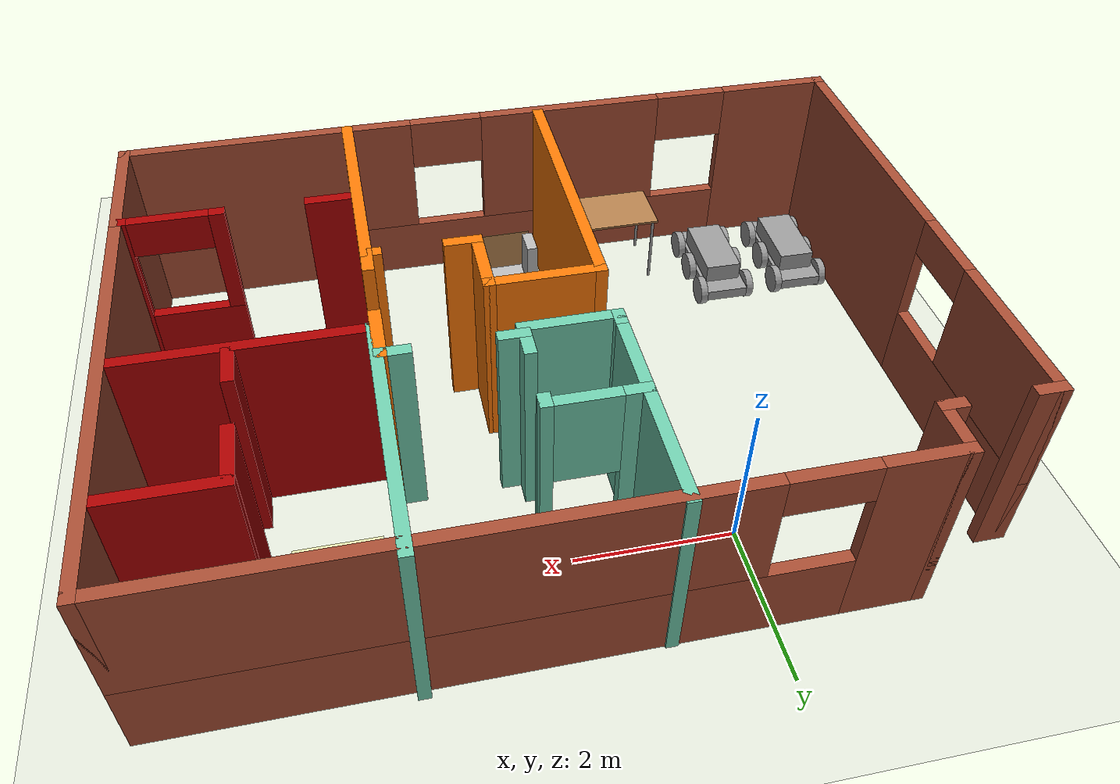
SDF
<sdf version="1.6">
 <world name="default">
  <plugin name="welcome_message" filename="libwelcome_message.so"/>
  <light name="sun" type="directional">
   <pose>0 0 10 0 -0 0</pose>
   <diffuse>0.8 0.8 0.8 1</diffuse>
   <specular>0.2 0.2 0.2 1</specular>
   <attenuation>
    <range>1000</range>
    <constant>0.9</constant>
    <linear>0.01</linear>
    <quadratic>0.001</quadratic>
   </attenuation>
   <direction>-0.5 0.1 -0.9</direction>
  </light>
  <model name="ground_plane">
   <static>1</static>
   <link name="link">
    <collision name="collision">
     <geometry><plane><normal>0 0 1</normal><size>100 100</size></plane></geometry>
     <surface><friction><ode><mu>100</mu><mu2>50</mu2></ode></friction></surface>
    </collision>
    <visual name="visual">
     <cast_shadows>0</cast_shadows>
     <geometry><plane><normal>0 0 1</normal><size>100 100</size></plane></geometry>
     <material>
      <script><uri>file://media/materials/scripts/gazebo.material</uri><name>Gazebo/Grey</name></script>
     </material>
    </visual>
   </link>
  </model>
  <gravity>0 0 -9.8</gravity>
  <magnetic_field>6e-06 2.3e-05 -4.2e-05</magnetic_field>
  <atmosphere type="adiabatic"/>
  <physics name="default_physics" default="0" type="ode">
   <max_step_size>0.001</max_step_size>
   <real_time_factor>1</real_time_factor>
   <real_time_update_rate>1000</real_time_update_rate>
  </physics>
  <scene><ambient>0.4 0.4 0.4 1</ambient><background>0.7 0.7 0.7 1</background><shadows>1</shadows></scene>
  <spherical_coordinates>
   <surface_model>EARTH_WGS84</surface_model>
   <latitude_deg>0</latitude_deg>
   <longitude_deg>0</longitude_deg>
   <elevation>0</elevation>
   <heading_deg>0</heading_deg>
  </spherical_coordinates>
  <model name="Building">
   <pose>1.9017 -2.33053 0 0 -0 0</pose>
   <link name="Wall_0">
    <pose>-4.30016 2.9635 0 0 -0 0</pose>
    <visual name="Wall_0_Visual_0">
     <pose>-0.550505 0 1.25 0 -0 0</pose>
     <geometry><box><size>0.39899 0.15 2.5</size></box></geometry>
     <material>
      <script><uri>file://media/materials/scripts/gazebo.material</uri><name>Gazebo/Bricks</name></script>
      <ambient>0.666667 0 0 1</ambient>
     </material>
     <meta><layer>0</layer></meta>
    </visual>
    <collision name="Wall_0_Collision_0">
     <geometry><box><size>0.39899 0.15 2.5</size></box></geometry>
     <pose>-0.550505 0 1.25 0 -0 0</pose>
    </collision>
    <visual name="Wall_0_Visual_1">
     <pose>0.581495 0 1.25 0 -0 0</pose>
     <geometry><box><size>0.33701 0.15 2.5</size></box></geometry>
     <material>
      <script><uri>file://media/materials/scripts/gazebo.material</uri><name>Gazebo/Bricks</name></script>
      <ambient>0.666667 0 0 1</ambient>
     </material>
     <meta><layer>0</layer></meta>
    </visual>
    <collision name="Wall_0_Collision_1">
     <geometry><box><size>0.33701 0.15 2.5</size></box></geometry>
     <pose>0.581495 0 1.25 0 -0 0</pose>
    </collision>
   </link>
   <link name="Wall_1">
    <collision name="Wall_1_Collision">
     <geometry><box><size>0.75 0.15 2.5</size></box></geometry>
     <pose>0 0 1.25 0 -0 0</pose>
    </collision>
    <visual name="Wall_1_Visual">
     <pose>0 0 1.25 0 -0 0</pose>
     <geometry><box><size>0.75 0.15 2.5</size></box></geometry>
     <material>
      <script><uri>file://media/materials/scripts/gazebo.material</uri><name>Gazebo/Bricks</name></script>
      <ambient>0.666667 0 0 1</ambient>
     </material>
     <meta><layer>0</layer></meta>
    </visual>
    <pose>-3.62515 3.2635 0 0 -0 1.5708</pose>
   </link>
   <link name="Wall_11">
    <pose>0.391864 1.53887 0 0 -0 1.5708</pose>
    <visual name="Wall_11_Visual_0">
     <pose>-0.412394 0 1.25 0 -0 0</pose>
     <geometry><box><size>0.425213 0.15 2.5</size></box></geometry>
     <material>
      <script><uri>file://media/materials/scripts/gazebo.material</uri><name>Gazebo/Grey</name></script>
      <ambient>0.435294 0.796078 0.67451 1</ambient>
     </material>
     <meta><layer>0</layer></meta>
    </visual>
    <collision name="Wall_11_Collision_0">
     <geometry><box><size>0.425213 0.15 2.5</size></box></geometry>
     <pose>-0.412394 0 1.25 0 -0 0</pose>
    </collision>
    <visual name="Wall_11_Visual_1">
     <pose>0.515606 0 1.25 0 -0 0</pose>
     <geometry><box><size>0.218787 0.15 2.5</size></box></geometry>
     <material>
      <script><uri>file://media/materials/scripts/gazebo.material</uri><name>Gazebo/Grey</name></script>
      <ambient>0.435294 0.796078 0.67451 1</ambient>
     </material>
     <meta><layer>0</layer></meta>
    </visual>
    <collision name="Wall_11_Collision_1">
     <geometry><box><size>0.218787 0.15 2.5</size></box></geometry>
     <pose>0.515606 0 1.25 0 -0 0</pose>
    </collision>
   </link>
   <link name="Wall_12">
    <pose>-0.158136 2.08887 0 0 -0 3.14159</pose>
    <visual name="Wall_12_Visual_0">
     <pose>-0.568138 0 1.25 0 -0 0</pose>
     <geometry><box><size>0.113724 0.15 2.5</size></box></geometry>
     <material>
      <script><uri>file://media/materials/scripts/gazebo.material</uri><name>Gazebo/Grey</name></script>
      <ambient>0.435294 0.796078 0.67451 1</ambient>
     </material>
     <meta><layer>0</layer></meta>
    </visual>
    <collision name="Wall_12_Collision_0">
     <geometry><box><size>0.113724 0.15 2.5</size></box></geometry>
     <pose>-0.568138 0 1.25 0 -0 0</pose>
    </collision>
    <visual name="Wall_12_Visual_1">
     <pose>0.056862 0 0.25 0 -0 0</pose>
     <geometry><box><size>1.13628 0.15 0.5</size></box></geometry>
     <material>
      <script><uri>file://media/materials/scripts/gazebo.material</uri><name>Gazebo/Grey</name></script>
      <ambient>0.435294 0.796078 0.67451 1</ambient>
     </material>
     <meta><layer>0</layer></meta>
    </visual>
    <collision name="Wall_12_Collision_1">
     <geometry><box><size>1.13628 0.15 0.5</size></box></geometry>
     <pose>0.056862 0 0.25 0 -0 0</pose>
    </collision>
    <visual name="Wall_12_Visual_2">
     <pose>0.456862 0 1.5 0 -0 0</pose>
     <geometry><box><size>0.336276 0.15 2</size></box></geometry>
     <material>
      <script><uri>file://media/materials/scripts/gazebo.material</uri><name>Gazebo/Grey</name></script>
      <ambient>0.435294 0.796078 0.67451 1</ambient>
     </material>
     <meta><layer>0</layer></meta>
    </visual>
    <collision name="Wall_12_Collision_2">
     <geometry><box><size>0.336276 0.15 2</size></box></geometry>
     <pose>0.456862 0 1.5 0 -0 0</pose>
    </collision>
    <visual name="Wall_12_Visual_3">
     <pose>-0.111276 0 1.9 0 -0 0</pose>
     <geometry><box><size>0.8 0.15 1.2</size></box></geometry>
     <material>
      <script><uri>file://media/materials/scripts/gazebo.material</uri><name>Gazebo/Grey</name></script>
      <ambient>0.435294 0.796078 0.67451 1</ambient>
     </material>
     <meta><layer>0</layer></meta>
    </visual>
    <collision name="Wall_12_Collision_3">
     <geometry><box><size>0.8 0.15 1.2</size></box></geometry>
     <pose>-0.111276 0 1.9 0 -0 0</pose>
    </collision>
   </link>
   <link name="Wall_16">
    <pose>1.19186 0.988869 0 0 -0 0</pose>
    <visual name="Wall_16_Visual_0">
     <pose>-0.680281 0 1.25 0 -0 0</pose>
     <geometry><box><size>0.389438 0.15 2.5</size></box></geometry>
     <material>
      <script><uri>file://media/materials/scripts/gazebo.material</uri><name>Gazebo/Grey</name></script>
      <ambient>0.435294 0.796078 0.67451 1</ambient>
     </material>
     <meta><layer>0</layer></meta>
    </visual>
    <collision name="Wall_16_Collision_0">
     <geometry><box><size>0.389438 0.15 2.5</size></box></geometry>
     <pose>-0.680281 0 1.25 0 -0 0</pose>
    </collision>
    <visual name="Wall_16_Visual_1">
     <pose>0.663744 0 1.25 0 -0 0</pose>
     <geometry><box><size>0.422512 0.15 2.5</size></box></geometry>
     <material>
      <script><uri>file://media/materials/scripts/gazebo.material</uri><name>Gazebo/Grey</name></script>
      <ambient>0.435294 0.796078 0.67451 1</ambient>
     </material>
     <meta><layer>0</layer></meta>
    </visual>
    <collision name="Wall_16_Collision_1">
     <geometry><box><size>0.422512 0.15 2.5</size></box></geometry>
     <pose>0.663744 0 1.25 0 -0 0</pose>
    </collision>
   </link>
   <link name="Wall_18">
    <collision name="Wall_18_Collision">
     <geometry><box><size>0.25 0.15 2.5</size></box></geometry>
     <pose>0 0 1.25 0 -0 0</pose>
    </collision>
    <visual name="Wall_18_Visual">
     <pose>0 0 1.25 0 -0 0</pose>
     <geometry><box><size>0.25 0.15 2.5</size></box></geometry>
     <material>
      <script><uri>file://media/materials/scripts/gazebo.material</uri><name>Gazebo/Grey</name></script>
      <ambient>0.435294 0.796078 0.67451 1</ambient>
     </material>
     <meta><layer>0</layer></meta>
    </visual>
    <pose>-0.708136 0.938869 0 0 0 -1.5708</pose>
   </link>
   <link name="Wall_19">
    <collision name="Wall_19_Collision">
     <geometry><box><size>1.25 0.15 2.5</size></box></geometry>
     <pose>0 0 1.25 0 -0 0</pose>
    </collision>
    <visual name="Wall_19_Visual">
     <pose>0 0 1.25 0 -0 0</pose>
     <geometry><box><size>1.25 0.15 2.5</size></box></geometry>
     <material>
      <script><uri>file://media/materials/scripts/gazebo.material</uri><name>Gazebo/Grey</name></script>
      <ambient>0.435294 0.796078 0.67451 1</ambient>
     </material>
     <meta><layer>0</layer></meta>
    </visual>
    <pose>-0.158136 0.888869 0 0 -0 0</pose>
   </link>
   <link name="Wall_2">
    <pose>0.674845 3.5635 0 0 -0 0</pose>
    <visual name="Wall_2_Visual_0">
     <pose>-3.86007 0 1.25 0 -0 0</pose>
     <geometry><box><size>1.02985 0.15 2.5</size></box></geometry>
     <material>
      <script><uri>file://media/materials/scripts/gazebo.material</uri><name>Gazebo/Bricks</name></script>
      <ambient>0.666667 0 0 1</ambient>
     </material>
     <meta><layer>0</layer></meta>
    </visual>
    <collision name="Wall_2_Collision_0">
     <geometry><box><size>1.02985 0.15 2.5</size></box></geometry>
     <pose>-3.86007 0 1.25 0 -0 0</pose>
    </collision>
    <visual name="Wall_2_Visual_1">
     <pose>0.514926 0 0.5 0 -0 0</pose>
     <geometry><box><size>7.72015 0.15 1</size></box></geometry>
     <material>
      <script><uri>file://media/materials/scripts/gazebo.material</uri><name>Gazebo/Bricks</name></script>
      <ambient>0.666667 0 0 1</ambient>
     </material>
     <meta><layer>0</layer></meta>
    </visual>
    <collision name="Wall_2_Collision_1">
     <geometry><box><size>7.72015 0.15 1</size></box></geometry>
     <pose>0.514926 0 0.5 0 -0 0</pose>
    </collision>
    <visual name="Wall_2_Visual_2">
     <pose>1.01493 0 1.75 0 -0 0</pose>
     <geometry><box><size>6.72015 0.15 1.5</size></box></geometry>
     <material>
      <script><uri>file://media/materials/scripts/gazebo.material</uri><name>Gazebo/Bricks</name></script>
      <ambient>0.666667 0 0 1</ambient>
     </material>
     <meta><layer>0</layer></meta>
    </visual>
    <collision name="Wall_2_Collision_2">
     <geometry><box><size>6.72015 0.15 1.5</size></box></geometry>
     <pose>1.01493 0 1.75 0 -0 0</pose>
    </collision>
    <visual name="Wall_2_Visual_3">
     <pose>-2.84515 0 2.25 0 -0 0</pose>
     <geometry><box><size>1 0.15 0.5</size></box></geometry>
     <material>
      <script><uri>file://media/materials/scripts/gazebo.material</uri><name>Gazebo/Bricks</name></script>
      <ambient>0.666667 0 0 1</ambient>
     </material>
     <meta><layer>0</layer></meta>
    </visual>
    <collision name="Wall_2_Collision_3">
     <geometry><box><size>1 0.15 0.5</size></box></geometry>
     <pose>-2.84515 0 2.25 0 -0 0</pose>
    </collision>
   </link>
   <link name="Wall_3">
    <collision name="Wall_3_Collision">
     <geometry><box><size>5.75 0.15 2.5</size></box></geometry>
     <pose>0 0 1.25 0 -0 0</pose>
    </collision>
    <visual name="Wall_3_Visual">
     <pose>0 0 1.25 0 -0 0</pose>
     <geometry><box><size>5.75 0.15 2.5</size></box></geometry>
     <material>
      <script><uri>file://media/materials/scripts/gazebo.material</uri><name>Gazebo/Bricks</name></script>
      <ambient>0.666667 0 0 1</ambient>
     </material>
     <meta><layer>0</layer></meta>
    </visual>
    <pose>4.97485 0.7635 0 0 0 -1.5708</pose>
   </link>
   <link name="Wall_37">
    <collision name="Wall_37_Collision">
     <geometry><box><size>3.25 0.15 2.5</size></box></geometry>
     <pose>0 0 1.25 0 -0 0</pose>
    </collision>
    <visual name="Wall_37_Visual">
     <pose>0 0 1.25 0 -0 0</pose>
     <geometry><box><size>3.25 0.15 2.5</size></box></geometry>
     <material>
      <script><uri>file://media/materials/scripts/gazebo.material</uri><name>Gazebo/Grey</name></script>
      <ambient>0.435294 0.796078 0.67451 1</ambient>
     </material>
     <meta><layer>0</layer></meta>
    </visual>
    <pose>2.03032 2.10888 0 0 0 -1.5708</pose>
   </link>
   <link name="Wall_39">
    <collision name="Wall_39_Collision">
     <geometry><box><size>3.75 0.15 2.5</size></box></geometry>
     <pose>0 0 1.25 0 -0 0</pose>
    </collision>
    <visual name="Wall_39_Visual">
     <pose>0 0 1.25 0 -0 0</pose>
     <geometry><box><size>3.75 0.15 2.5</size></box></geometry>
     <material>
      <script><uri>file://media/materials/scripts/gazebo.material</uri><name>Gazebo/Grey</name></script>
      <ambient>0.996078 0.47451 0.0196078 1</ambient>
     </material>
     <meta><layer>0</layer></meta>
    </visual>
    <pose>-0.719298 -1.75833 0 0 -0 1.5708</pose>
   </link>
   <link name="Wall_4">
    <pose>3.54984 -2.0365 0 0 -0 3.14159</pose>
    <visual name="Wall_4_Visual_0">
     <pose>-1.40037 0 1.25 0 -0 0</pose>
     <geometry><box><size>0.199251 0.15 2.5</size></box></geometry>
     <material>
      <script><uri>file://media/materials/scripts/gazebo.material</uri><name>Gazebo/Grey</name></script>
      <ambient>0.666667 0 0 1</ambient>
     </material>
     <meta><layer>0</layer></meta>
    </visual>
    <collision name="Wall_4_Collision_0">
     <geometry><box><size>0.199251 0.15 2.5</size></box></geometry>
     <pose>-1.40037 0 1.25 0 -0 0</pose>
    </collision>
    <visual name="Wall_4_Visual_1">
     <pose>1.1996 0 1.25 0 -0 0</pose>
     <geometry><box><size>0.600792 0.15 2.5</size></box></geometry>
     <material>
      <script><uri>file://media/materials/scripts/gazebo.material</uri><name>Gazebo/Grey</name></script>
      <ambient>0.666667 0 0 1</ambient>
     </material>
     <meta><layer>0</layer></meta>
    </visual>
    <collision name="Wall_4_Collision_1">
     <geometry><box><size>0.600792 0.15 2.5</size></box></geometry>
     <pose>1.1996 0 1.25 0 -0 0</pose>
    </collision>
    <visual name="Wall_4_Visual_2">
     <pose>-0.70027 0 0.5 0 -0 0</pose>
     <geometry><box><size>1.20096 0.15 1</size></box></geometry>
     <material>
      <script><uri>file://media/materials/scripts/gazebo.material</uri><name>Gazebo/Grey</name></script>
      <ambient>0.666667 0 0 1</ambient>
     </material>
     <meta><layer>0</layer></meta>
    </visual>
    <collision name="Wall_4_Collision_2">
     <geometry><box><size>1.20096 0.15 1</size></box></geometry>
     <pose>-0.70027 0 0.5 0 -0 0</pose>
    </collision>
    <visual name="Wall_4_Visual_3">
     <pose>-0.20027 0 1.75 0 -0 0</pose>
     <geometry><box><size>0.200957 0.15 1.5</size></box></geometry>
     <material>
      <script><uri>file://media/materials/scripts/gazebo.material</uri><name>Gazebo/Grey</name></script>
      <ambient>0.666667 0 0 1</ambient>
     </material>
     <meta><layer>0</layer></meta>
    </visual>
    <collision name="Wall_4_Collision_3">
     <geometry><box><size>0.200957 0.15 1.5</size></box></geometry>
     <pose>-0.20027 0 1.75 0 -0 0</pose>
    </collision>
    <visual name="Wall_4_Visual_4">
     <pose>-0.800749 0 2.25 0 -0 0</pose>
     <geometry><box><size>1 0.15 0.5</size></box></geometry>
     <material>
      <script><uri>file://media/materials/scripts/gazebo.material</uri><name>Gazebo/Grey</name></script>
      <ambient>0.666667 0 0 1</ambient>
     </material>
     <meta><layer>0</layer></meta>
    </visual>
    <collision name="Wall_4_Collision_4">
     <geometry><box><size>1 0.15 0.5</size></box></geometry>
     <pose>-0.800749 0 2.25 0 -0 0</pose>
    </collision>
   </link>
   <link name="Wall_50">
    <collision name="Wall_50_Collision">
     <geometry><box><size>1.5 0.15 2.5</size></box></geometry>
     <pose>0 0 1.25 0 -0 0</pose>
    </collision>
    <visual name="Wall_50_Visual">
     <pose>0 0 1.25 0 -0 0</pose>
     <geometry><box><size>1.5 0.15 2.5</size></box></geometry>
     <material>
      <script><uri>file://media/materials/scripts/gazebo.material</uri><name>Gazebo/Grey</name></script>
      <ambient>0.996078 0.47451 0.0196078 1</ambient>
     </material>
     <meta><layer>0</layer></meta>
    </visual>
    <pose>-0.044298 0.041665 0 0 -0 0</pose>
   </link>
   <link name="Wall_51">
    <collision name="Wall_51_Collision">
     <geometry><box><size>1 0.15 2.5</size></box></geometry>
     <pose>0 0 1.25 0 -0 0</pose>
    </collision>
    <visual name="Wall_51_Visual">
     <pose>0 0 1.25 0 -0 0</pose>
     <geometry><box><size>1 0.15 2.5</size></box></geometry>
     <material>
      <script><uri>file://media/materials/scripts/gazebo.material</uri><name>Gazebo/Grey</name></script>
      <ambient>0.996078 0.47451 0.0196078 1</ambient>
     </material>
     <meta><layer>0</layer></meta>
    </visual>
    <pose>0.630702 -0.383335 0 0 0 -1.5708</pose>
   </link>
   <link name="Wall_52">
    <pose>1.3057 -0.808335 0 0 -0 0</pose>
    <visual name="Wall_52_Visual_0">
     <pose>-0.504705 0 1.25 0 -0 0</pose>
     <geometry><box><size>0.490591 0.15 2.5</size></box></geometry>
     <material>
      <script><uri>file://media/materials/scripts/gazebo.material</uri><name>Gazebo/Grey</name></script>
      <ambient>0.996078 0.47451 0.0196078 1</ambient>
     </material>
     <meta><layer>0</layer></meta>
    </visual>
    <collision name="Wall_52_Collision_0">
     <geometry><box><size>0.490591 0.15 2.5</size></box></geometry>
     <pose>-0.504705 0 1.25 0 -0 0</pose>
    </collision>
    <visual name="Wall_52_Visual_1">
     <pose>0.617295 0 1.25 0 -0 0</pose>
     <geometry><box><size>0.265409 0.15 2.5</size></box></geometry>
     <material>
      <script><uri>file://media/materials/scripts/gazebo.material</uri><name>Gazebo/Grey</name></script>
      <ambient>0.996078 0.47451 0.0196078 1</ambient>
     </material>
     <meta><layer>0</layer></meta>
    </visual>
    <collision name="Wall_52_Collision_1">
     <geometry><box><size>0.265409 0.15 2.5</size></box></geometry>
     <pose>0.617295 0 1.25 0 -0 0</pose>
    </collision>
   </link>
   <link name="Wall_54">
    <collision name="Wall_54_Collision">
     <geometry><box><size>3 0.15 2.5</size></box></geometry>
     <pose>0 0 1.25 0 -0 0</pose>
    </collision>
    <visual name="Wall_54_Visual">
     <pose>0 0 1.25 0 -0 0</pose>
     <geometry><box><size>3 0.15 2.5</size></box></geometry>
     <material>
      <script><uri>file://media/materials/scripts/gazebo.material</uri><name>Gazebo/Grey</name></script>
      <ambient>0.996078 0.47451 0.0196078 1</ambient>
     </material>
     <meta><layer>0</layer></meta>
    </visual>
    <pose>1.9807 -2.23333 0 0 0 -1.5708</pose>
   </link>
   <link name="Wall_56">
    <pose>-1.49723 -3.64742 0 0 0 -0.003139</pose>
    <visual name="Wall_56_Visual_0">
     <pose>-2.77726 0 1.25 0 -0 0</pose>
     <geometry><box><size>1.55137 0.15 2.5</size></box></geometry>
     <material>
      <script><uri>file://media/materials/scripts/gazebo.material</uri><name>Gazebo/Bricks</name></script>
      <ambient>0.666667 0 0 1</ambient>
     </material>
     <meta><layer>0</layer></meta>
    </visual>
    <collision name="Wall_56_Collision_0">
     <geometry><box><size>1.55137 0.15 2.5</size></box></geometry>
     <pose>-2.77726 0 1.25 0 -0 0</pose>
    </collision>
    <visual name="Wall_56_Visual_1">
     <pose>0.775684 0 0.4 0 -0 0</pose>
     <geometry><box><size>5.55452 0.15 0.8</size></box></geometry>
     <material>
      <script><uri>file://media/materials/scripts/gazebo.material</uri><name>Gazebo/Bricks</name></script>
      <ambient>0.666667 0 0 1</ambient>
     </material>
     <meta><layer>0</layer></meta>
    </visual>
    <collision name="Wall_56_Collision_1">
     <geometry><box><size>5.55452 0.15 0.8</size></box></geometry>
     <pose>0.775684 0 0.4 0 -0 0</pose>
    </collision>
    <visual name="Wall_56_Visual_2">
     <pose>0.299823 0 1.65 0 -0 0</pose>
     <geometry><box><size>2.6028 0.15 1.7</size></box></geometry>
     <material>
      <script><uri>file://media/materials/scripts/gazebo.material</uri><name>Gazebo/Bricks</name></script>
      <ambient>0.666667 0 0 1</ambient>
     </material>
     <meta><layer>0</layer></meta>
    </visual>
    <collision name="Wall_56_Collision_2">
     <geometry><box><size>2.6028 0.15 1.7</size></box></geometry>
     <pose>0.299823 0 1.65 0 -0 0</pose>
    </collision>
    <visual name="Wall_56_Visual_3">
     <pose>3.07708 0 1.65 0 -0 0</pose>
     <geometry><box><size>0.951723 0.15 1.7</size></box></geometry>
     <material>
      <script><uri>file://media/materials/scripts/gazebo.material</uri><name>Gazebo/Bricks</name></script>
      <ambient>0.666667 0 0 1</ambient>
     </material>
     <meta><layer>0</layer></meta>
    </visual>
    <collision name="Wall_56_Collision_3">
     <geometry><box><size>0.951723 0.15 1.7</size></box></geometry>
     <pose>3.07708 0 1.65 0 -0 0</pose>
    </collision>
    <visual name="Wall_56_Visual_4">
     <pose>-1.50158 0 2.15 0 -0 0</pose>
     <geometry><box><size>1 0.15 0.7</size></box></geometry>
     <material>
      <script><uri>file://media/materials/scripts/gazebo.material</uri><name>Gazebo/Bricks</name></script>
      <ambient>0.666667 0 0 1</ambient>
     </material>
     <meta><layer>0</layer></meta>
    </visual>
    <collision name="Wall_56_Collision_4">
     <geometry><box><size>1 0.15 0.7</size></box></geometry>
     <pose>-1.50158 0 2.15 0 -0 0</pose>
    </collision>
    <visual name="Wall_56_Visual_5">
     <pose>2.10122 0 2.15 0 -0 0</pose>
     <geometry><box><size>1 0.15 0.7</size></box></geometry>
     <material>
      <script><uri>file://media/materials/scripts/gazebo.material</uri><name>Gazebo/Bricks</name></script>
      <ambient>0.666667 0 0 1</ambient>
     </material>
     <meta><layer>0</layer></meta>
    </visual>
    <collision name="Wall_56_Collision_5">
     <geometry><box><size>1 0.15 0.7</size></box></geometry>
     <pose>2.10122 0 2.15 0 -0 0</pose>
    </collision>
   </link>
   <link name="Wall_58">
    <pose>1.98628 0.090267 0 0 -0 1.56458</pose>
    <visual name="Wall_58_Visual_0">
     <pose>-0.761715 0 1.25 0 -0 0</pose>
     <geometry><box><size>0.423808 0.15 2.5</size></box></geometry>
     <material>
      <script><uri>file://media/materials/scripts/gazebo.material</uri><name>Gazebo/Grey</name></script>
      <ambient>0.996078 0.47451 0.0196078 1</ambient>
     </material>
     <meta><layer>0</layer></meta>
    </visual>
    <collision name="Wall_58_Collision_0">
     <geometry><box><size>0.423808 0.15 2.5</size></box></geometry>
     <pose>-0.761715 0 1.25 0 -0 0</pose>
    </collision>
    <visual name="Wall_58_Visual_1">
     <pose>0.577384 0 1.25 0 -0 0</pose>
     <geometry><box><size>0.792471 0.15 2.5</size></box></geometry>
     <material>
      <script><uri>file://media/materials/scripts/gazebo.material</uri><name>Gazebo/Grey</name></script>
      <ambient>0.996078 0.47451 0.0196078 1</ambient>
     </material>
     <meta><layer>0</layer></meta>
    </visual>
    <collision name="Wall_58_Collision_1">
     <geometry><box><size>0.792471 0.15 2.5</size></box></geometry>
     <pose>0.577384 0 1.25 0 -0 0</pose>
    </collision>
   </link>
   <link name="Wall_60">
    <collision name="Wall_60_Collision">
     <geometry><box><size>1.75 0.15 2.5</size></box></geometry>
     <pose>0 0 1.25 0 -0 0</pose>
    </collision>
    <visual name="Wall_60_Visual">
     <pose>0 0 1.25 0 -0 0</pose>
     <geometry><box><size>1.75 0.15 2.5</size></box></geometry>
     <material>
      <script><uri>file://media/materials/scripts/gazebo.material</uri><name>Gazebo/Bricks</name></script>
      <ambient>0.666667 0 0 1</ambient>
     </material>
     <meta><layer>0</layer></meta>
    </visual>
    <pose>4.97485 -2.8365 0 0 0 -1.5708</pose>
   </link>
   <link name="Wall_61">
    <collision name="Wall_61_Collision">
     <geometry><box><size>3.14422 0.15 2.5</size></box></geometry>
     <pose>0 0 1.25 0 -0 0</pose>
    </collision>
    <visual name="Wall_61_Visual">
     <pose>0 0 1.25 0 -0 0</pose>
     <geometry><box><size>3.14422 0.15 2.5</size></box></geometry>
     <material>
      <script><uri>file://media/materials/scripts/gazebo.material</uri><name>Gazebo/Bricks</name></script>
      <ambient>0.666667 0 0 1</ambient>
     </material>
     <meta><layer>0</layer></meta>
    </visual>
    <pose>3.47777 -3.64742 0 0 0 -3.1343</pose>
   </link>
   <link name="Wall_63">
    <collision name="Wall_63_Collision">
     <geometry><box><size>1.5 0.15 2.5</size></box></geometry>
     <pose>0 0 1.25 0 -0 0</pose>
    </collision>
    <visual name="Wall_63_Visual">
     <pose>0 0 1.25 0 -0 0</pose>
     <geometry><box><size>1.5 0.15 2.5</size></box></geometry>
     <material>
      <script><uri>file://media/materials/scripts/gazebo.material</uri><name>Gazebo/Grey</name></script>
      <ambient>0.666667 0 0 1</ambient>
     </material>
     <meta><layer>0</layer></meta>
    </visual>
    <pose>4.28835 2.48996 0 0 -0 3.14159</pose>
   </link>
   <link name="Wall_64">
    <pose>3.61335 1.56496 0 0 0 -1.5708</pose>
    <visual name="Wall_64_Visual_0">
     <pose>-0.582062 0 1.25 0 -0 0</pose>
     <geometry><box><size>0.835877 0.15 2.5</size></box></geometry>
     <material>
      <script><uri>file://media/materials/scripts/gazebo.material</uri><name>Gazebo/Grey</name></script>
      <ambient>0.666667 0 0 1</ambient>
     </material>
     <meta><layer>0</layer></meta>
    </visual>
    <collision name="Wall_64_Collision_0">
     <geometry><box><size>0.835877 0.15 2.5</size></box></geometry>
     <pose>-0.582062 0 1.25 0 -0 0</pose>
    </collision>
    <visual name="Wall_64_Visual_1">
     <pose>0.727938 0 1.25 0 -0 0</pose>
     <geometry><box><size>0.544123 0.15 2.5</size></box></geometry>
     <material>
      <script><uri>file://media/materials/scripts/gazebo.material</uri><name>Gazebo/Grey</name></script>
      <ambient>0.666667 0 0 1</ambient>
     </material>
     <meta><layer>0</layer></meta>
    </visual>
    <collision name="Wall_64_Collision_1">
     <geometry><box><size>0.544123 0.15 2.5</size></box></geometry>
     <pose>0.727938 0 1.25 0 -0 0</pose>
    </collision>
   </link>
   <link name="Wall_66">
    <collision name="Wall_66_Collision">
     <geometry><box><size>3 0.15 2.5</size></box></geometry>
     <pose>0 0 1.25 0 -0 0</pose>
    </collision>
    <visual name="Wall_66_Visual">
     <pose>0 0 1.25 0 -0 0</pose>
     <geometry><box><size>3 0.15 2.5</size></box></geometry>
     <material>
      <script><uri>file://media/materials/scripts/gazebo.material</uri><name>Gazebo/Grey</name></script>
      <ambient>0.666667 0 0 1</ambient>
     </material>
     <meta><layer>0</layer></meta>
    </visual>
    <pose>3.45533 0.55888 0 0 -0 0</pose>
   </link>
   <link name="Wall_7">
    <pose>-4.97515 -0.3365 0 0 -0 1.5708</pose>
    <visual name="Wall_7_Visual_0">
     <pose>-1.53025 0 1.25 0 -0 0</pose>
     <geometry><box><size>3.6895 0.15 2.5</size></box></geometry>
     <material>
      <script><uri>file://media/materials/scripts/gazebo.material</uri><name>Gazebo/Bricks</name></script>
      <ambient>0.666667 0 0 1</ambient>
     </material>
     <meta><layer>0</layer></meta>
    </visual>
    <collision name="Wall_7_Collision_0">
     <geometry><box><size>3.6895 0.15 2.5</size></box></geometry>
     <pose>-1.53025 0 1.25 0 -0 0</pose>
    </collision>
    <visual name="Wall_7_Visual_1">
     <pose>1.84475 0 0.5 0 -0 0</pose>
     <geometry><box><size>3.0605 0.15 1</size></box></geometry>
     <material>
      <script><uri>file://media/materials/scripts/gazebo.material</uri><name>Gazebo/Bricks</name></script>
      <ambient>0.666667 0 0 1</ambient>
     </material>
     <meta><layer>0</layer></meta>
    </visual>
    <collision name="Wall_7_Collision_1">
     <geometry><box><size>3.0605 0.15 1</size></box></geometry>
     <pose>1.84475 0 0.5 0 -0 0</pose>
    </collision>
    <visual name="Wall_7_Visual_2">
     <pose>2.34475 0 1.75 0 -0 0</pose>
     <geometry><box><size>2.0605 0.15 1.5</size></box></geometry>
     <material>
      <script><uri>file://media/materials/scripts/gazebo.material</uri><name>Gazebo/Bricks</name></script>
      <ambient>0.666667 0 0 1</ambient>
     </material>
     <meta><layer>0</layer></meta>
    </visual>
    <collision name="Wall_7_Collision_2">
     <geometry><box><size>2.0605 0.15 1.5</size></box></geometry>
     <pose>2.34475 0 1.75 0 -0 0</pose>
    </collision>
    <visual name="Wall_7_Visual_3">
     <pose>0.814501 0 2.25 0 -0 0</pose>
     <geometry><box><size>1 0.15 0.5</size></box></geometry>
     <material>
      <script><uri>file://media/materials/scripts/gazebo.material</uri><name>Gazebo/Bricks</name></script>
      <ambient>0.666667 0 0 1</ambient>
     </material>
     <meta><layer>0</layer></meta>
    </visual>
    <collision name="Wall_7_Collision_3">
     <geometry><box><size>1 0.15 0.5</size></box></geometry>
     <pose>0.814501 0 2.25 0 -0 0</pose>
    </collision>
   </link>
   <link name="Wall_9">
    <collision name="Wall_9_Collision">
     <geometry><box><size>2.75 0.15 2.5</size></box></geometry>
     <pose>0 0 1.25 0 -0 0</pose>
    </collision>
    <visual name="Wall_9_Visual">
     <pose>0 0 1.25 0 -0 0</pose>
     <geometry><box><size>2.75 0.15 2.5</size></box></geometry>
     <material>
      <script><uri>file://media/materials/scripts/gazebo.material</uri><name>Gazebo/Grey</name></script>
      <ambient>0.435294 0.796078 0.67451 1</ambient>
     </material>
     <meta><layer>0</layer></meta>
    </visual>
    <pose>-0.708136 2.28887 0 0 0 -1.5708</pose>
   </link>
   <static>1</static>
  </model>
  <model name="Humanoid_Robot">
   <link name="link_0">
    <pose>0 -0.004307 -0.025 0 -0 0</pose>
    <inertial>
     <mass>1</mass>
     <inertia>
      <ixx>0.166667</ixx>
      <ixy>0</ixy>
      <ixz>0</ixz>
      <iyy>0.166667</iyy>
      <iyz>0</iyz>
      <izz>0.166667</izz>
     </inertia>
    </inertial>
    <visual name="visual">
     <geometry><box><size>0.6 1.5 0.15</size></box></geometry>
     <material>
      <lighting>1</lighting>
      <script><uri>file://media/materials/scripts/gazebo.material</uri><name>Gazebo/Grey</name></script>
      <shader type="pixel"><normal_map>__default__</normal_map></shader>
      <ambient>0.3 0.3 0.3 1</ambient>
      <diffuse>0.7 0.7 0.7 1</diffuse>
      <specular>0.01 0.01 0.01 1</specular>
      <emissive>0 0 0 1</emissive>
     </material>
    </visual>
    <collision name="collision">
     <geometry><box><size>0.6 1.5 0.15</size></box></geometry>
     <surface>
      <friction>
       <ode><mu>1</mu><mu2>1</mu2><fdir1>0 0 0</fdir1><slip1>0</slip1><slip2>0</slip2></ode>
       <torsional>
        <coefficient>1</coefficient>
        <patch_radius>0</patch_radius>
        <surface_radius>0</surface_radius>
        <use_patch_radius>1</use_patch_radius>
        <ode><slip>0</slip></ode>
       </torsional>
      </friction>
      <bounce><restitution_coefficient>0</restitution_coefficient><threshold>1e+06</threshold></bounce>
      <contact>
       <collide_without_contact>0</collide_without_contact>
       <collide_without_contact_bitmask>1</collide_without_contact_bitmask>
       <collide_bitmask>1</collide_bitmask>
       <ode>
        <soft_cfm>0</soft_cfm>
        <soft_erp>0.2</soft_erp>
        <kp>1e+13</kp>
        <kd>1</kd>
        <max_vel>0.01</max_vel>
        <min_depth>0</min_depth>
       </ode>
       <bullet>
        <split_impulse>1</split_impulse>
        <split_impulse_penetration_threshold>-0.01</split_impulse_penetration_threshold>
        <soft_cfm>0</soft_cfm>
        <soft_erp>0.2</soft_erp>
        <kp>1e+13</kp>
        <kd>1</kd>
       </bullet>
      </contact>
     </surface>
    </collision>
   </link>
   <link name="link_1_clone">
    <pose>-0.351854 0.545219 -0.025 1.57079 -9.6e-05 -1.56152</pose>
    <inertial>
     <mass>1</mass>
     <inertia><ixx>0.145833</ixx><ixy>0</ixy><ixz>0</ixz><iyy>0.145833</iyy><iyz>0</iyz><izz>0.125</izz></inertia>
    </inertial>
    <visual name="visual">
     <geometry><cylinder><radius>0.2</radius><length>0.1</length></cylinder></geometry>
     <material>
      <lighting>1</lighting>
      <script><uri>file://media/materials/scripts/gazebo.material</uri><name>Gazebo/Grey</name></script>
      <shader type="pixel"><normal_map>__default__</normal_map></shader>
      <ambient>0.3 0.3 0.3 1</ambient>
      <diffuse>0.7 0.7 0.7 1</diffuse>
      <specular>0.01 0.01 0.01 1</specular>
      <emissive>0 0 0 1</emissive>
     </material>
    </visual>
    <collision name="collision">
     <geometry><cylinder><radius>0.2</radius><length>0.1</length></cylinder></geometry>
     <surface>
      <friction>
       <ode><mu>1</mu><mu2>1</mu2><fdir1>0 0 0</fdir1><slip1>0</slip1><slip2>0</slip2></ode>
       <torsional>
        <coefficient>1</coefficient>
        <patch_radius>0</patch_radius>
        <surface_radius>0</surface_radius>
        <use_patch_radius>1</use_patch_radius>
        <ode><slip>0</slip></ode>
       </torsional>
      </friction>
      <bounce><restitution_coefficient>0</restitution_coefficient><threshold>1e+06</threshold></bounce>
      <contact>
       <collide_without_contact>0</collide_without_contact>
       <collide_without_contact_bitmask>1</collide_without_contact_bitmask>
       <collide_bitmask>1</collide_bitmask>
       <ode>
        <soft_cfm>0</soft_cfm>
        <soft_erp>0.2</soft_erp>
        <kp>1e+13</kp>
        <kd>1</kd>
        <max_vel>0.01</max_vel>
        <min_depth>0</min_depth>
       </ode>
       <bullet>
        <split_impulse>1</split_impulse>
        <split_impulse_penetration_threshold>-0.01</split_impulse_penetration_threshold>
        <soft_cfm>0</soft_cfm>
        <soft_erp>0.2</soft_erp>
        <kp>1e+13</kp>
        <kd>1</kd>
       </bullet>
      </contact>
     </surface>
    </collision>
   </link>
   <link name="link_1_clone_0">
    <pose>-0.351854 -0.553832 -0.025 1.57079 -9.6e-05 -1.56152</pose>
    <inertial>
     <mass>1</mass>
     <inertia><ixx>0.145833</ixx><ixy>0</ixy><ixz>0</ixz><iyy>0.145833</iyy><iyz>0</iyz><izz>0.125</izz></inertia>
    </inertial>
    <visual name="visual">
     <geometry><cylinder><radius>0.2</radius><length>0.1</length></cylinder></geometry>
     <material>
      <lighting>1</lighting>
      <script><uri>file://media/materials/scripts/gazebo.material</uri><name>Gazebo/Grey</name></script>
      <shader type="pixel"><normal_map>__default__</normal_map></shader>
      <ambient>0.3 0.3 0.3 1</ambient>
      <diffuse>0.7 0.7 0.7 1</diffuse>
      <specular>0.01 0.01 0.01 1</specular>
      <emissive>0 0 0 1</emissive>
     </material>
    </visual>
    <collision name="collision">
     <geometry><cylinder><radius>0.2</radius><length>0.1</length></cylinder></geometry>
     <surface>
      <friction>
       <ode><mu>1</mu><mu2>1</mu2><fdir1>0 0 0</fdir1><slip1>0</slip1><slip2>0</slip2></ode>
       <torsional>
        <coefficient>1</coefficient>
        <patch_radius>0</patch_radius>
        <surface_radius>0</surface_radius>
        <use_patch_radius>1</use_patch_radius>
        <ode><slip>0</slip></ode>
       </torsional>
      </friction>
      <bounce><restitution_coefficient>0</restitution_coefficient><threshold>1e+06</threshold></bounce>
      <contact>
       <collide_without_contact>0</collide_without_contact>
       <collide_without_contact_bitmask>1</collide_without_contact_bitmask>
       <collide_bitmask>1</collide_bitmask>
       <ode>
        <soft_cfm>0</soft_cfm>
        <soft_erp>0.2</soft_erp>
        <kp>1e+13</kp>
        <kd>1</kd>
        <max_vel>0.01</max_vel>
        <min_depth>0</min_depth>
       </ode>
       <bullet>
        <split_impulse>1</split_impulse>
        <split_impulse_penetration_threshold>-0.01</split_impulse_penetration_threshold>
        <soft_cfm>0</soft_cfm>
        <soft_erp>0.2</soft_erp>
        <kp>1e+13</kp>
        <kd>1</kd>
       </bullet>
      </contact>
     </surface>
    </collision>
   </link>
   <link name="link_1_clone_1">
    <pose>0.351854 0.579674 -0.025 1.57079 -9.6e-05 -1.56152</pose>
    <inertial>
     <mass>1</mass>
     <inertia><ixx>0.145833</ixx><ixy>0</ixy><ixz>0</ixz><iyy>0.145833</iyy><iyz>0</iyz><izz>0.125</izz></inertia>
    </inertial>
    <visual name="visual">
     <geometry><cylinder><radius>0.2</radius><length>0.1</length></cylinder></geometry>
     <material>
      <lighting>1</lighting>
      <script><uri>file://media/materials/scripts/gazebo.material</uri><name>Gazebo/Grey</name></script>
      <shader type="pixel"><normal_map>__default__</normal_map></shader>
      <ambient>0.3 0.3 0.3 1</ambient>
      <diffuse>0.7 0.7 0.7 1</diffuse>
      <specular>0.01 0.01 0.01 1</specular>
      <emissive>0 0 0 1</emissive>
     </material>
    </visual>
    <collision name="collision">
     <geometry><cylinder><radius>0.2</radius><length>0.1</length></cylinder></geometry>
     <surface>
      <friction>
       <ode><mu>1</mu><mu2>1</mu2><fdir1>0 0 0</fdir1><slip1>0</slip1><slip2>0</slip2></ode>
       <torsional>
        <coefficient>1</coefficient>
        <patch_radius>0</patch_radius>
        <surface_radius>0</surface_radius>
        <use_patch_radius>1</use_patch_radius>
        <ode><slip>0</slip></ode>
       </torsional>
      </friction>
      <bounce><restitution_coefficient>0</restitution_coefficient><threshold>1e+06</threshold></bounce>
      <contact>
       <collide_without_contact>0</collide_without_contact>
       <collide_without_contact_bitmask>1</collide_without_contact_bitmask>
       <collide_bitmask>1</collide_bitmask>
       <ode>
        <soft_cfm>0</soft_cfm>
        <soft_erp>0.2</soft_erp>
        <kp>1e+13</kp>
        <kd>1</kd>
        <max_vel>0.01</max_vel>
        <min_depth>0</min_depth>
       </ode>
       <bullet>
        <split_impulse>1</split_impulse>
        <split_impulse_penetration_threshold>-0.01</split_impulse_penetration_threshold>
        <soft_cfm>0</soft_cfm>
        <soft_erp>0.2</soft_erp>
        <kp>1e+13</kp>
        <kd>1</kd>
       </bullet>
      </contact>
     </surface>
    </collision>
   </link>
   <link name="link_1_clone_1_clone">
    <pose>0.351854 -0.004307 -0.025 1.57079 -9.6e-05 -1.56152</pose>
    <inertial>
     <mass>1</mass>
     <inertia><ixx>0.145833</ixx><ixy>0</ixy><ixz>0</ixz><iyy>0.145833</iyy><iyz>0</iyz><izz>0.125</izz></inertia>
    </inertial>
    <visual name="visual">
     <geometry><cylinder><radius>0.2</radius><length>0.1</length></cylinder></geometry>
     <material>
      <lighting>1</lighting>
      <script><uri>file://media/materials/scripts/gazebo.material</uri><name>Gazebo/Grey</name></script>
      <shader type="pixel"><normal_map>__default__</normal_map></shader>
      <ambient>0.3 0.3 0.3 1</ambient>
      <diffuse>0.7 0.7 0.7 1</diffuse>
      <specular>0.01 0.01 0.01 1</specular>
      <emissive>0 0 0 1</emissive>
     </material>
    </visual>
    <collision name="collision">
     <geometry><cylinder><radius>0.2</radius><length>0.1</length></cylinder></geometry>
     <surface>
      <friction>
       <ode><mu>1</mu><mu2>1</mu2><fdir1>0 0 0</fdir1><slip1>0</slip1><slip2>0</slip2></ode>
       <torsional>
        <coefficient>1</coefficient>
        <patch_radius>0</patch_radius>
        <surface_radius>0</surface_radius>
        <use_patch_radius>1</use_patch_radius>
        <ode><slip>0</slip></ode>
       </torsional>
      </friction>
      <bounce><restitution_coefficient>0</restitution_coefficient><threshold>1e+06</threshold></bounce>
      <contact>
       <collide_without_contact>0</collide_without_contact>
       <collide_without_contact_bitmask>1</collide_without_contact_bitmask>
       <collide_bitmask>1</collide_bitmask>
       <ode>
        <soft_cfm>0</soft_cfm>
        <soft_erp>0.2</soft_erp>
        <kp>1e+13</kp>
        <kd>1</kd>
        <max_vel>0.01</max_vel>
        <min_depth>0</min_depth>
       </ode>
       <bullet>
        <split_impulse>1</split_impulse>
        <split_impulse_penetration_threshold>-0.01</split_impulse_penetration_threshold>
        <soft_cfm>0</soft_cfm>
        <soft_erp>0.2</soft_erp>
        <kp>1e+13</kp>
        <kd>1</kd>
       </bullet>
      </contact>
     </surface>
    </collision>
   </link>
   <link name="link_1_clone_2">
    <pose>-0.351854 -0.004307 -0.025 1.57079 -9.6e-05 -1.56152</pose>
    <inertial>
     <mass>1</mass>
     <inertia><ixx>0.145833</ixx><ixy>0</ixy><ixz>0</ixz><iyy>0.145833</iyy><iyz>0</iyz><izz>0.125</izz></inertia>
    </inertial>
    <visual name="visual">
     <geometry><cylinder><radius>0.2</radius><length>0.1</length></cylinder></geometry>
     <material>
      <lighting>1</lighting>
      <script><uri>file://media/materials/scripts/gazebo.material</uri><name>Gazebo/Grey</name></script>
      <shader type="pixel"><normal_map>__default__</normal_map></shader>
      <ambient>0.3 0.3 0.3 1</ambient>
      <diffuse>0.7 0.7 0.7 1</diffuse>
      <specular>0.01 0.01 0.01 1</specular>
      <emissive>0 0 0 1</emissive>
     </material>
    </visual>
    <collision name="collision">
     <geometry><cylinder><radius>0.2</radius><length>0.1</length></cylinder></geometry>
     <surface>
      <friction>
       <ode><mu>1</mu><mu2>1</mu2><fdir1>0 0 0</fdir1><slip1>0</slip1><slip2>0</slip2></ode>
       <torsional>
        <coefficient>1</coefficient>
        <patch_radius>0</patch_radius>
        <surface_radius>0</surface_radius>
        <use_patch_radius>1</use_patch_radius>
        <ode><slip>0</slip></ode>
       </torsional>
      </friction>
      <bounce><restitution_coefficient>0</restitution_coefficient><threshold>1e+06</threshold></bounce>
      <contact>
       <collide_without_contact>0</collide_without_contact>
       <collide_without_contact_bitmask>1</collide_without_contact_bitmask>
       <collide_bitmask>1</collide_bitmask>
       <ode>
        <soft_cfm>0</soft_cfm>
        <soft_erp>0.2</soft_erp>
        <kp>1e+13</kp>
        <kd>1</kd>
        <max_vel>0.01</max_vel>
        <min_depth>0</min_depth>
       </ode>
       <bullet>
        <split_impulse>1</split_impulse>
        <split_impulse_penetration_threshold>-0.01</split_impulse_penetration_threshold>
        <soft_cfm>0</soft_cfm>
        <soft_erp>0.2</soft_erp>
        <kp>1e+13</kp>
        <kd>1</kd>
       </bullet>
      </contact>
     </surface>
    </collision>
   </link>
   <link name="link_1_clone_3">
    <pose>0.351854 -0.553832 -0.025 1.57079 -9.6e-05 -1.56152</pose>
    <inertial>
     <mass>1</mass>
     <inertia><ixx>0.145833</ixx><ixy>0</ixy><ixz>0</ixz><iyy>0.145833</iyy><iyz>0</iyz><izz>0.125</izz></inertia>
    </inertial>
    <visual name="visual">
     <geometry><cylinder><radius>0.2</radius><length>0.1</length></cylinder></geometry>
     <material>
      <lighting>1</lighting>
      <script><uri>file://media/materials/scripts/gazebo.material</uri><name>Gazebo/Grey</name></script>
      <shader type="pixel"><normal_map>__default__</normal_map></shader>
      <ambient>0.3 0.3 0.3 1</ambient>
      <diffuse>0.7 0.7 0.7 1</diffuse>
      <specular>0.01 0.01 0.01 1</specular>
      <emissive>0 0 0 1</emissive>
     </material>
    </visual>
    <collision name="collision">
     <geometry><cylinder><radius>0.2</radius><length>0.1</length></cylinder></geometry>
     <surface>
      <friction>
       <ode><mu>1</mu><mu2>1</mu2><fdir1>0 0 0</fdir1><slip1>0</slip1><slip2>0</slip2></ode>
       <torsional>
        <coefficient>1</coefficient>
        <patch_radius>0</patch_radius>
        <surface_radius>0</surface_radius>
        <use_patch_radius>1</use_patch_radius>
        <ode><slip>0</slip></ode>
       </torsional>
      </friction>
      <bounce><restitution_coefficient>0</restitution_coefficient><threshold>1e+06</threshold></bounce>
      <contact>
       <collide_without_contact>0</collide_without_contact>
       <collide_without_contact_bitmask>1</collide_without_contact_bitmask>
       <collide_bitmask>1</collide_bitmask>
       <ode>
        <soft_cfm>0</soft_cfm>
        <soft_erp>0.2</soft_erp>
        <kp>1e+13</kp>
        <kd>1</kd>
        <max_vel>0.01</max_vel>
        <min_depth>0</min_depth>
       </ode>
       <bullet>
        <split_impulse>1</split_impulse>
        <split_impulse_penetration_threshold>-0.01</split_impulse_penetration_threshold>
        <soft_cfm>0</soft_cfm>
        <soft_erp>0.2</soft_erp>
        <kp>1e+13</kp>
        <kd>1</kd>
       </bullet>
      </contact>
     </surface>
    </collision>
   </link>
   <link name="link_2">
    <pose>0 -0.004307 0.175 0 -0 0</pose>
    <inertial>
     <mass>1</mass>
     <inertia>
      <ixx>0.166667</ixx>
      <ixy>0</ixy>
      <ixz>0</ixz>
      <iyy>0.166667</iyy>
      <iyz>0</iyz>
      <izz>0.166667</izz>
     </inertia>
    </inertial>
    <visual name="visual">
     <geometry><box><size>0.5 1 0.27</size></box></geometry>
     <material>
      <lighting>1</lighting>
      <script><uri>file://media/materials/scripts/gazebo.material</uri><name>Gazebo/Grey</name></script>
      <shader type="pixel"><normal_map>__default__</normal_map></shader>
      <ambient>0.3 0.3 0.3 1</ambient>
      <diffuse>0.7 0.7 0.7 1</diffuse>
      <specular>0.01 0.01 0.01 1</specular>
      <emissive>0 0 0 1</emissive>
     </material>
    </visual>
    <collision name="collision">
     <geometry><box><size>0.5 1 0.3</size></box></geometry>
     <surface>
      <friction>
       <ode><mu>1</mu><mu2>1</mu2><fdir1>0 0 0</fdir1><slip1>0</slip1><slip2>0</slip2></ode>
       <torsional>
        <coefficient>1</coefficient>
        <patch_radius>0</patch_radius>
        <surface_radius>0</surface_radius>
        <use_patch_radius>1</use_patch_radius>
        <ode><slip>0</slip></ode>
       </torsional>
      </friction>
      <bounce><restitution_coefficient>0</restitution_coefficient><threshold>1e+06</threshold></bounce>
      <contact>
       <collide_without_contact>0</collide_without_contact>
       <collide_without_contact_bitmask>1</collide_without_contact_bitmask>
       <collide_bitmask>1</collide_bitmask>
       <ode>
        <soft_cfm>0</soft_cfm>
        <soft_erp>0.2</soft_erp>
        <kp>1e+13</kp>
        <kd>1</kd>
        <max_vel>0.01</max_vel>
        <min_depth>0</min_depth>
       </ode>
       <bullet>
        <split_impulse>1</split_impulse>
        <split_impulse_penetration_threshold>-0.01</split_impulse_penetration_threshold>
        <soft_cfm>0</soft_cfm>
        <soft_erp>0.2</soft_erp>
        <kp>1e+13</kp>
        <kd>1</kd>
       </bullet>
      </contact>
     </surface>
    </collision>
   </link>
   <joint name="link_0_JOINT_0" type="revolute">
    <parent>link_0</parent>
    <child>link_1_clone_0</child>
    <axis>
     <xyz>0 0 1</xyz>
     <use_parent_model_frame>0</use_parent_model_frame>
     <limit>
      <lower>-1.79769e+308</lower>
      <upper>1.79769e+308</upper>
      <effort>-1</effort>
      <velocity>-1</velocity>
     </limit>
     <dynamics>
      <spring_reference>0</spring_reference>
      <spring_stiffness>0</spring_stiffness>
      <damping>0</damping>
     </dynamics>
    </axis>
    <physics>
     <ode><limit><cfm>0</cfm><erp>0.2</erp></limit><suspension><cfm>0</cfm><erp>0.2</erp></suspension></ode>
    </physics>
   </joint>
   <joint name="link_0_JOINT_10" type="revolute">
    <parent>link_0</parent>
    <child>link_1_clone_1_clone</child>
    <axis>
     <xyz>0 0 -1</xyz>
     <use_parent_model_frame>0</use_parent_model_frame>
     <limit>
      <lower>-1.79769e+308</lower>
      <upper>1.79769e+308</upper>
      <effort>-1</effort>
      <velocity>-1</velocity>
     </limit>
     <dynamics>
      <spring_reference>0</spring_reference>
      <spring_stiffness>0</spring_stiffness>
      <damping>0</damping>
     </dynamics>
    </axis>
    <physics>
     <ode><limit><cfm>0</cfm><erp>0.2</erp></limit><suspension><cfm>0</cfm><erp>0.2</erp></suspension></ode>
    </physics>
   </joint>
   <joint name="link_0_JOINT_2" type="revolute">
    <parent>link_0</parent>
    <child>link_1_clone_3</child>
    <axis>
     <xyz>0 0 -1</xyz>
     <use_parent_model_frame>0</use_parent_model_frame>
     <limit>
      <lower>-1.79769e+308</lower>
      <upper>1.79769e+308</upper>
      <effort>-1</effort>
      <velocity>-1</velocity>
     </limit>
     <dynamics>
      <spring_reference>0</spring_reference>
      <spring_stiffness>0</spring_stiffness>
      <damping>0</damping>
     </dynamics>
    </axis>
    <physics>
     <ode><limit><cfm>0</cfm><erp>0.2</erp></limit><suspension><cfm>0</cfm><erp>0.2</erp></suspension></ode>
    </physics>
   </joint>
   <joint name="link_0_JOINT_3" type="revolute">
    <parent>link_0</parent>
    <child>link_1_clone_1</child>
    <axis>
     <xyz>0 0 -1</xyz>
     <use_parent_model_frame>0</use_parent_model_frame>
     <limit>
      <lower>-1.79769e+308</lower>
      <upper>1.79769e+308</upper>
      <effort>-1</effort>
      <velocity>-1</velocity>
     </limit>
     <dynamics>
      <spring_reference>0</spring_reference>
      <spring_stiffness>0</spring_stiffness>
      <damping>0</damping>
     </dynamics>
    </axis>
    <physics>
     <ode><limit><cfm>0</cfm><erp>0.2</erp></limit><suspension><cfm>0</cfm><erp>0.2</erp></suspension></ode>
    </physics>
   </joint>
   <joint name="link_0_JOINT_4" type="revolute">
    <parent>link_0</parent>
    <child>link_1_clone</child>
    <axis>
     <xyz>0 0 1</xyz>
     <use_parent_model_frame>0</use_parent_model_frame>
     <limit>
      <lower>-1.79769e+308</lower>
      <upper>1.79769e+308</upper>
      <effort>-1</effort>
      <velocity>-1</velocity>
     </limit>
     <dynamics>
      <spring_reference>0</spring_reference>
      <spring_stiffness>0</spring_stiffness>
      <damping>0</damping>
     </dynamics>
    </axis>
    <physics>
     <ode><limit><cfm>0</cfm><erp>0.2</erp></limit><suspension><cfm>0</cfm><erp>0.2</erp></suspension></ode>
    </physics>
   </joint>
   <joint name="link_0_JOINT_6" type="revolute">
    <parent>link_0</parent>
    <child>link_1_clone_2</child>
    <axis>
     <xyz>0 0 1</xyz>
     <use_parent_model_frame>0</use_parent_model_frame>
     <limit>
      <lower>-1.79769e+308</lower>
      <upper>1.79769e+308</upper>
      <effort>-1</effort>
      <velocity>-1</velocity>
     </limit>
     <dynamics>
      <spring_reference>0</spring_reference>
      <spring_stiffness>0</spring_stiffness>
      <damping>0</damping>
     </dynamics>
    </axis>
    <physics>
     <ode><limit><cfm>0</cfm><erp>0.2</erp></limit><suspension><cfm>0</cfm><erp>0.2</erp></suspension></ode>
    </physics>
   </joint>
   <static>0</static>
   <pose>-1.30239 -4.82109 0.224998 0 6e-06 -0.008391</pose>
  </model>
  <model name="table">
   <static>1</static>
   <link name="link">
    <collision name="surface">
     <pose>0 0 1 0 -0 0</pose>
     <geometry><box><size>1.5 0.8 0.03</size></box></geometry>
     <surface><friction><ode><mu>0.6</mu><mu2>0.6</mu2></ode></friction></surface>
    </collision>
    <visual name="visual1">
     <pose>0 0 1 0 -0 0</pose>
     <geometry><box><size>1.5 0.8 0.03</size></box></geometry>
     <material>
      <script><uri>file://media/materials/scripts/gazebo.material</uri><name>Gazebo/Wood</name></script>
     </material>
    </visual>
    <collision name="front_left_leg">
     <pose>0.68 0.38 0.5 0 -0 0</pose>
     <geometry><cylinder><radius>0.02</radius><length>1</length></cylinder></geometry>
    </collision>
    <visual name="front_left_leg">
     <pose>0.68 0.38 0.5 0 -0 0</pose>
     <geometry><cylinder><radius>0.02</radius><length>1</length></cylinder></geometry>
     <material>
      <script><uri>file://media/materials/scripts/gazebo.material</uri><name>Gazebo/Grey</name></script>
     </material>
    </visual>
    <collision name="front_right_leg">
     <pose>0.68 -0.38 0.5 0 -0 0</pose>
     <geometry><cylinder><radius>0.02</radius><length>1</length></cylinder></geometry>
    </collision>
    <visual name="front_right_leg">
     <pose>0.68 -0.38 0.5 0 -0 0</pose>
     <geometry><cylinder><radius>0.02</radius><length>1</length></cylinder></geometry>
     <material>
      <script><uri>file://media/materials/scripts/gazebo.material</uri><name>Gazebo/Grey</name></script>
     </material>
    </visual>
    <collision name="back_right_leg">
     <pose>-0.68 -0.38 0.5 0 -0 0</pose>
     <geometry><cylinder><radius>0.02</radius><length>1</length></cylinder></geometry>
    </collision>
    <visual name="back_right_leg">
     <pose>-0.68 -0.38 0.5 0 -0 0</pose>
     <geometry><cylinder><radius>0.02</radius><length>1</length></cylinder></geometry>
     <material>
      <script><uri>file://media/materials/scripts/gazebo.material</uri><name>Gazebo/Grey</name></script>
     </material>
    </visual>
    <collision name="back_left_leg">
     <pose>-0.68 0.38 0.5 0 -0 0</pose>
     <geometry><cylinder><radius>0.02</radius><length>1</length></cylinder></geometry>
    </collision>
    <visual name="back_left_leg">
     <pose>-0.68 0.38 0.5 0 -0 0</pose>
     <geometry><cylinder><radius>0.02</radius><length>1</length></cylinder></geometry>
     <material>
      <script><uri>file://media/materials/scripts/gazebo.material</uri><name>Gazebo/Grey</name></script>
     </material>
    </visual>
   </link>
   <pose>0.313078 -5.37194 0 0 -0 0</pose>
  </model>
  <model name="cabinet">
   <static>1</static>
   <link name="cabinet_bottom_plate">
    <inertial>
     <pose>0 0 -1 0 -0 0</pose>
     <inertia><ixx>2.05</ixx><ixy>0</ixy><ixz>0</ixz><iyy>2.05</iyy><iyz>0</iyz><izz>2.05</izz></inertia>
     <mass>25</mass>
    </inertial>
    <collision name="cabinet_bottom_plate_geom">
     <pose>0 0 0.01 0 -0 0</pose>
     <geometry><box><size>0.45 0.45 0.02</size></box></geometry>
    </collision>
    <visual name="cabinet_bottom_plate_geom_visual">
     <pose>0 0 0.01 0 -0 0</pose>
     <geometry><box><size>0.45 0.45 0.02</size></box></geometry>
     <material>
      <script><uri>file://media/materials/scripts/gazebo.material</uri><name>Gazebo/Wood</name></script>
     </material>
    </visual>
    <collision name="cabinet_bottom_plate_geom_cabinet_back_plate">
     <pose>0.235 0 0.51 0 -0 0</pose>
     <geometry><box><size>0.02 0.45 1.02</size></box></geometry>
    </collision>
    <visual name="cabinet_bottom_plate_geom_cabinet_back_plate_visual">
     <pose>0.235 0 0.51 0 -0 0</pose>
     <geometry><box><size>0.02 0.45 1.02</size></box></geometry>
     <material>
      <script><uri>file://media/materials/scripts/gazebo.material</uri><name>Gazebo/Wood</name></script>
     </material>
    </visual>
    <collision name="cabinet_bottom_plate_geom_cabinet_left_plate">
     <pose>0 0.235 0.51 0 -0 0</pose>
     <geometry><box><size>0.45 0.02 1.02</size></box></geometry>
    </collision>
    <visual name="cabinet_bottom_plate_geom_cabinet_left_plate_visual">
     <pose>0 0.235 0.51 0 -0 0</pose>
     <geometry><box><size>0.45 0.02 1.02</size></box></geometry>
     <material>
      <script><uri>file://media/materials/scripts/gazebo.material</uri><name>Gazebo/Wood</name></script>
     </material>
    </visual>
    <collision name="cabinet_bottom_plate_geom_cabinet_middle_plate">
     <pose>0 0 0.51 0 -0 0</pose>
     <geometry><box><size>0.45 0.45 0.02</size></box></geometry>
    </collision>
    <visual name="cabinet_bottom_plate_geom_cabinet_middle_plate_visual">
     <pose>0 0 0.51 0 -0 0</pose>
     <geometry><box><size>0.45 0.45 0.02</size></box></geometry>
     <material>
      <script><uri>file://media/materials/scripts/gazebo.material</uri><name>Gazebo/Wood</name></script>
     </material>
    </visual>
    <collision name="cabinet_bottom_plate_geom_cabinet_right_plate">
     <pose>0 -0.235 0.51 0 -0 0</pose>
     <geometry><box><size>0.45 0.02 1.02</size></box></geometry>
    </collision>
    <visual name="cabinet_bottom_plate_geom_cabinet_right_plate_visual">
     <pose>0 -0.235 0.51 0 -0 0</pose>
     <geometry><box><size>0.45 0.02 1.02</size></box></geometry>
     <material>
      <script><uri>file://media/materials/scripts/gazebo.material</uri><name>Gazebo/Wood</name></script>
     </material>
    </visual>
    <collision name="cabinet_bottom_plate_geom_cabinet_top_plate">
     <pose>0 0 1.01 0 -0 0</pose>
     <geometry><box><size>0.45 0.45 0.02</size></box></geometry>
    </collision>
    <visual name="cabinet_bottom_plate_geom_cabinet_top_plate_visual">
     <pose>0 0 1.01 0 -0 0</pose>
     <geometry><box><size>0.45 0.45 0.02</size></box></geometry>
     <material>
      <script><uri>file://media/materials/scripts/gazebo.material</uri><name>Gazebo/Wood</name></script>
     </material>
    </visual>
   </link>
   <pose>3.53679 0.899806 0 0 -0 1.55192</pose>
  </model>
  <model name="frc2016_sallyport">
   <link name="base">
    <inertial>
     <mass>50</mass>
     <pose>0 0 0.35406 0 -0 0</pose>
     <inertia><ixx>0.727808</ixx><ixy>0</ixy><ixz>0</ixz><iyy>1.77488</iyy><iyz>0</iyz><izz>1.64109</izz></inertia>
    </inertial>
    <visual name="platform">
     <pose>0 0 0.06974 0 -0 0</pose>
     <geometry><box><size>1.27 0.5969 0.003175</size></box></geometry>
    </visual>
    <collision name="platform">
     <pose>0 0 0.06974 0 -0 0</pose>
     <geometry><box><size>1.27 0.5969 0.003175</size></box></geometry>
    </collision>
    <visual name="left_column">
     <pose>-0.5588 0.00318 0.38876 0 -0 0</pose>
     <geometry><box><size>0.1524 0.38735 0.635</size></box></geometry>
    </visual>
    <collision name="left_column">
     <pose>-0.5588 0.00318 0.38876 0 -0 0</pose>
     <geometry><box><size>0.1524 0.38735 0.635</size></box></geometry>
    </collision>
    <visual name="right_column">
     <pose>0.6096 0.00635 0.38876 0 -0 0</pose>
     <geometry><box><size>0.0508 0.381 0.635</size></box></geometry>
    </visual>
    <collision name="right_column">
     <pose>0.6096 0.00635 0.38876 0 -0 0</pose>
     <geometry><box><size>0.0508 0.381 0.635</size></box></geometry>
    </collision>
    <visual name="castor1">
     <pose>-0.45886 0.15389 0.03487 0 -0 0</pose>
     <geometry><sphere><radius>0.03487</radius></sphere></geometry>
    </visual>
    <collision name="castor1">
     <pose>-0.45886 0.15389 0.03487 0 -0 0</pose>
     <geometry><sphere><radius>0.03487</radius></sphere></geometry>
    </collision>
    <visual name="castor2">
     <pose>-0.28117 -0.22559 0.03487 0 -0 0</pose>
     <geometry><sphere><radius>0.03487</radius></sphere></geometry>
    </visual>
    <collision name="castor2">
     <pose>-0.28117 -0.22559 0.03487 0 -0 0</pose>
     <geometry><sphere><radius>0.03487</radius></sphere></geometry>
    </collision>
    <visual name="castor3">
     <pose>0.27933 -0.2272 0.03487 0 -0 0</pose>
     <geometry><sphere><radius>0.03487</radius></sphere></geometry>
    </visual>
    <collision name="castor3">
     <pose>0.27933 -0.2272 0.03487 0 -0 0</pose>
     <geometry><sphere><radius>0.03487</radius></sphere></geometry>
    </collision>
    <visual name="castor4">
     <pose>0.4571 0.15424 0.03487 0 -0 0</pose>
     <geometry><sphere><radius>0.03487</radius></sphere></geometry>
    </visual>
    <collision name="castor4">
     <pose>0.4571 0.15424 0.03487 0 -0 0</pose>
     <geometry><sphere><radius>0.03487</radius></sphere></geometry>
    </collision>
   </link>
   <link name="door">
    <pose>0.02255 -0.24321 0.40332 0 -0 0</pose>
    <inertial>
     <pose>0 0 0 -1.5707 0 0</pose>
     <mass>2</mass>
     <inertia>
      <ixx>0.0619421</ixx>
      <ixy>0</ixy>
      <ixz>0</ixz>
      <iyy>0.246462</iyy>
      <iyz>0</iyz>
      <izz>0.30839</izz>
     </inertia>
    </inertial>
    <visual name="visual">
     <geometry><box><size>1.21603 0.00635 0.6096</size></box></geometry>
     <material><script><name>Gazebo/WoodFloor</name><uri>__default__</uri></script></material>
    </visual>
    <collision name="collision"><geometry><box><size>1.21603 0.00635 0.6096</size></box></geometry></collision>
   </link>
   <joint name="door_joint" type="revolute">
    <pose>-0.608015 0 0 0 -0 0</pose>
    <parent>base</parent>
    <child>door</child>
    <axis>
     <xyz>0 0 1</xyz>
     <limit><lower>-3.1415</lower><upper>0</upper></limit>
     <use_parent_model_frame>0</use_parent_model_frame>
     <dynamics><spring_reference>0</spring_reference><spring_stiffness>0</spring_stiffness></dynamics>
    </axis>
   </joint>
   <pose>1.9972 -5.27543 0 -2e-06 -0 0.012791</pose>
  </model>
  <model name="marble_1_5cm">
   <link name="link">
    <pose>0 0 0.0075 0 -0 0</pose>
    <inertial>
     <mass>0.0062</mass>
     <inertia>
      <ixx>1.395e-07</ixx>
      <ixy>0</ixy>
      <ixz>0</ixz>
      <iyy>1.395e-07</iyy>
      <iyz>0</iyz>
      <izz>1.395e-07</izz>
     </inertia>
    </inertial>
    <collision name="collision">
     <geometry><sphere><radius>0.0075</radius></sphere></geometry>
     <surface>
      <contact>
       <poissons_ratio>0.22</poissons_ratio>
       <elastic_modulus>5.1e+10</elastic_modulus>
       <ode><kp>100000</kp><kd>100</kd><max_vel>100</max_vel><min_depth>0.001</min_depth></ode>
      </contact>
      <friction>
       <torsional>
        <coefficient>1</coefficient>
        <use_patch_radius>0</use_patch_radius>
        <surface_radius>0.01</surface_radius>
       </torsional>
      </friction>
     </surface>
    </collision>
    <visual name="visual">
     <geometry><sphere><radius>0.0075</radius></sphere></geometry>
     <material>
      <script><uri>file://media/materials/scripts/gazebo.material</uri><name>Gazebo/Blue</name></script>
     </material>
    </visual>
    <velocity_decay><linear>0</linear><angular>0.005</angular></velocity_decay>
   </link>
   <pose>-2.74147 -4.33994 -0.001001 0 -0 0</pose>
  </model>
  <model name="RegionEventBox">
   <static>1</static>
   <pose>4.63342 0.358262 0 0 -0 0</pose>
   <link name="link">
    <visual name="visual">
     <transparency>0.75</transparency>
     <geometry><box><size>1 1 1.75</size></box></geometry>
     <material>
      <script><uri>file://media/materials/scripts/gazebo.material</uri><name>Gazebo/Yellow</name></script>
     </material>
    </visual>
   </link>
   <plugin name="region_event_box" filename="libRegionEventBoxPlugin.so">
    <event><name>model_in_region_event_box</name><type>inclusion</type><active>true</active></event>
   </plugin>
  </model>
  <model name="Humanoid_Robot_clone">
   <link name="link_0">
    <pose>0 -0.004307 -0.025 0 -0 0</pose>
    <inertial>
     <mass>1</mass>
     <inertia>
      <ixx>0.166667</ixx>
      <ixy>0</ixy>
      <ixz>0</ixz>
      <iyy>0.166667</iyy>
      <iyz>0</iyz>
      <izz>0.166667</izz>
     </inertia>
    </inertial>
    <visual name="visual">
     <geometry><box><size>0.6 1.5 0.15</size></box></geometry>
     <material>
      <lighting>1</lighting>
      <script><uri>file://media/materials/scripts/gazebo.material</uri><name>Gazebo/Grey</name></script>
      <shader type="pixel"><normal_map>__default__</normal_map></shader>
      <ambient>0.3 0.3 0.3 1</ambient>
      <diffuse>0.7 0.7 0.7 1</diffuse>
      <specular>0.01 0.01 0.01 1</specular>
      <emissive>0 0 0 1</emissive>
     </material>
    </visual>
    <collision name="collision">
     <geometry><box><size>0.6 1.5 0.15</size></box></geometry>
     <surface>
      <friction>
       <ode><mu>1</mu><mu2>1</mu2><fdir1>0 0 0</fdir1><slip1>0</slip1><slip2>0</slip2></ode>
       <torsional>
        <coefficient>1</coefficient>
        <patch_radius>0</patch_radius>
        <surface_radius>0</surface_radius>
        <use_patch_radius>1</use_patch_radius>
        <ode><slip>0</slip></ode>
       </torsional>
      </friction>
      <bounce><restitution_coefficient>0</restitution_coefficient><threshold>1e+06</threshold></bounce>
      <contact>
       <collide_without_contact>0</collide_without_contact>
       <collide_without_contact_bitmask>1</collide_without_contact_bitmask>
       <collide_bitmask>1</collide_bitmask>
       <ode>
        <soft_cfm>0</soft_cfm>
        <soft_erp>0.2</soft_erp>
        <kp>1e+13</kp>
        <kd>1</kd>
        <max_vel>0.01</max_vel>
        <min_depth>0</min_depth>
       </ode>
       <bullet>
        <split_impulse>1</split_impulse>
        <split_impulse_penetration_threshold>-0.01</split_impulse_penetration_threshold>
        <soft_cfm>0</soft_cfm>
        <soft_erp>0.2</soft_erp>
        <kp>1e+13</kp>
        <kd>1</kd>
       </bullet>
      </contact>
     </surface>
    </collision>
   </link>
   <link name="link_1_clone">
    <pose>-0.351854 0.545219 -0.025 1.57079 -9.6e-05 -1.56152</pose>
    <inertial>
     <mass>1</mass>
     <inertia><ixx>0.145833</ixx><ixy>0</ixy><ixz>0</ixz><iyy>0.145833</iyy><iyz>0</iyz><izz>0.125</izz></inertia>
    </inertial>
    <visual name="visual">
     <geometry><cylinder><radius>0.2</radius><length>0.1</length></cylinder></geometry>
     <material>
      <lighting>1</lighting>
      <script><uri>file://media/materials/scripts/gazebo.material</uri><name>Gazebo/Grey</name></script>
      <shader type="pixel"><normal_map>__default__</normal_map></shader>
      <ambient>0.3 0.3 0.3 1</ambient>
      <diffuse>0.7 0.7 0.7 1</diffuse>
      <specular>0.01 0.01 0.01 1</specular>
      <emissive>0 0 0 1</emissive>
     </material>
    </visual>
    <collision name="collision">
     <geometry><cylinder><radius>0.2</radius><length>0.1</length></cylinder></geometry>
     <surface>
      <friction>
       <ode><mu>1</mu><mu2>1</mu2><fdir1>0 0 0</fdir1><slip1>0</slip1><slip2>0</slip2></ode>
       <torsional>
        <coefficient>1</coefficient>
        <patch_radius>0</patch_radius>
        <surface_radius>0</surface_radius>
        <use_patch_radius>1</use_patch_radius>
        <ode><slip>0</slip></ode>
       </torsional>
      </friction>
      <bounce><restitution_coefficient>0</restitution_coefficient><threshold>1e+06</threshold></bounce>
      <contact>
       <collide_without_contact>0</collide_without_contact>
       <collide_without_contact_bitmask>1</collide_without_contact_bitmask>
       <collide_bitmask>1</collide_bitmask>
       <ode>
        <soft_cfm>0</soft_cfm>
        <soft_erp>0.2</soft_erp>
        <kp>1e+13</kp>
        <kd>1</kd>
        <max_vel>0.01</max_vel>
        <min_depth>0</min_depth>
       </ode>
       <bullet>
        <split_impulse>1</split_impulse>
        <split_impulse_penetration_threshold>-0.01</split_impulse_penetration_threshold>
        <soft_cfm>0</soft_cfm>
        <soft_erp>0.2</soft_erp>
        <kp>1e+13</kp>
        <kd>1</kd>
       </bullet>
      </contact>
     </surface>
    </collision>
   </link>
   <link name="link_1_clone_0">
    <pose>-0.351854 -0.553832 -0.025 1.57079 -9.6e-05 -1.56152</pose>
    <inertial>
     <mass>1</mass>
     <inertia><ixx>0.145833</ixx><ixy>0</ixy><ixz>0</ixz><iyy>0.145833</iyy><iyz>0</iyz><izz>0.125</izz></inertia>
    </inertial>
    <visual name="visual">
     <geometry><cylinder><radius>0.2</radius><length>0.1</length></cylinder></geometry>
     <material>
      <lighting>1</lighting>
      <script><uri>file://media/materials/scripts/gazebo.material</uri><name>Gazebo/Grey</name></script>
      <shader type="pixel"><normal_map>__default__</normal_map></shader>
      <ambient>0.3 0.3 0.3 1</ambient>
      <diffuse>0.7 0.7 0.7 1</diffuse>
      <specular>0.01 0.01 0.01 1</specular>
      <emissive>0 0 0 1</emissive>
     </material>
    </visual>
    <collision name="collision">
     <geometry><cylinder><radius>0.2</radius><length>0.1</length></cylinder></geometry>
     <surface>
      <friction>
       <ode><mu>1</mu><mu2>1</mu2><fdir1>0 0 0</fdir1><slip1>0</slip1><slip2>0</slip2></ode>
       <torsional>
        <coefficient>1</coefficient>
        <patch_radius>0</patch_radius>
        <surface_radius>0</surface_radius>
        <use_patch_radius>1</use_patch_radius>
        <ode><slip>0</slip></ode>
       </torsional>
      </friction>
      <bounce><restitution_coefficient>0</restitution_coefficient><threshold>1e+06</threshold></bounce>
      <contact>
       <collide_without_contact>0</collide_without_contact>
       <collide_without_contact_bitmask>1</collide_without_contact_bitmask>
       <collide_bitmask>1</collide_bitmask>
       <ode>
        <soft_cfm>0</soft_cfm>
        <soft_erp>0.2</soft_erp>
        <kp>1e+13</kp>
        <kd>1</kd>
        <max_vel>0.01</max_vel>
        <min_depth>0</min_depth>
       </ode>
       <bullet>
        <split_impulse>1</split_impulse>
        <split_impulse_penetration_threshold>-0.01</split_impulse_penetration_threshold>
        <soft_cfm>0</soft_cfm>
        <soft_erp>0.2</soft_erp>
        <kp>1e+13</kp>
        <kd>1</kd>
       </bullet>
      </contact>
     </surface>
    </collision>
   </link>
   <link name="link_1_clone_1">
    <pose>0.351854 0.579674 -0.025 1.57079 -9.6e-05 -1.56152</pose>
    <inertial>
     <mass>1</mass>
     <inertia><ixx>0.145833</ixx><ixy>0</ixy><ixz>0</ixz><iyy>0.145833</iyy><iyz>0</iyz><izz>0.125</izz></inertia>
    </inertial>
    <visual name="visual">
     <geometry><cylinder><radius>0.2</radius><length>0.1</length></cylinder></geometry>
     <material>
      <lighting>1</lighting>
      <script><uri>file://media/materials/scripts/gazebo.material</uri><name>Gazebo/Grey</name></script>
      <shader type="pixel"><normal_map>__default__</normal_map></shader>
      <ambient>0.3 0.3 0.3 1</ambient>
      <diffuse>0.7 0.7 0.7 1</diffuse>
      <specular>0.01 0.01 0.01 1</specular>
      <emissive>0 0 0 1</emissive>
     </material>
    </visual>
    <collision name="collision">
     <geometry><cylinder><radius>0.2</radius><length>0.1</length></cylinder></geometry>
     <surface>
      <friction>
       <ode><mu>1</mu><mu2>1</mu2><fdir1>0 0 0</fdir1><slip1>0</slip1><slip2>0</slip2></ode>
       <torsional>
        <coefficient>1</coefficient>
        <patch_radius>0</patch_radius>
        <surface_radius>0</surface_radius>
        <use_patch_radius>1</use_patch_radius>
        <ode><slip>0</slip></ode>
       </torsional>
      </friction>
      <bounce><restitution_coefficient>0</restitution_coefficient><threshold>1e+06</threshold></bounce>
      <contact>
       <collide_without_contact>0</collide_without_contact>
       <collide_without_contact_bitmask>1</collide_without_contact_bitmask>
       <collide_bitmask>1</collide_bitmask>
       <ode>
        <soft_cfm>0</soft_cfm>
        <soft_erp>0.2</soft_erp>
        <kp>1e+13</kp>
        <kd>1</kd>
        <max_vel>0.01</max_vel>
        <min_depth>0</min_depth>
       </ode>
       <bullet>
        <split_impulse>1</split_impulse>
        <split_impulse_penetration_threshold>-0.01</split_impulse_penetration_threshold>
        <soft_cfm>0</soft_cfm>
        <soft_erp>0.2</soft_erp>
        <kp>1e+13</kp>
        <kd>1</kd>
       </bullet>
      </contact>
     </surface>
    </collision>
   </link>
   <link name="link_1_clone_1_clone">
    <pose>0.351854 -0.004307 -0.025 1.57079 -9.6e-05 -1.56152</pose>
    <inertial>
     <mass>1</mass>
     <inertia><ixx>0.145833</ixx><ixy>0</ixy><ixz>0</ixz><iyy>0.145833</iyy><iyz>0</iyz><izz>0.125</izz></inertia>
    </inertial>
    <visual name="visual">
     <geometry><cylinder><radius>0.2</radius><length>0.1</length></cylinder></geometry>
     <material>
      <lighting>1</lighting>
      <script><uri>file://media/materials/scripts/gazebo.material</uri><name>Gazebo/Grey</name></script>
      <shader type="pixel"><normal_map>__default__</normal_map></shader>
      <ambient>0.3 0.3 0.3 1</ambient>
      <diffuse>0.7 0.7 0.7 1</diffuse>
      <specular>0.01 0.01 0.01 1</specular>
      <emissive>0 0 0 1</emissive>
     </material>
    </visual>
    <collision name="collision">
     <geometry><cylinder><radius>0.2</radius><length>0.1</length></cylinder></geometry>
     <surface>
      <friction>
       <ode><mu>1</mu><mu2>1</mu2><fdir1>0 0 0</fdir1><slip1>0</slip1><slip2>0</slip2></ode>
       <torsional>
        <coefficient>1</coefficient>
        <patch_radius>0</patch_radius>
        <surface_radius>0</surface_radius>
        <use_patch_radius>1</use_patch_radius>
        <ode><slip>0</slip></ode>
       </torsional>
      </friction>
      <bounce><restitution_coefficient>0</restitution_coefficient><threshold>1e+06</threshold></bounce>
      <contact>
       <collide_without_contact>0</collide_without_contact>
       <collide_without_contact_bitmask>1</collide_without_contact_bitmask>
       <collide_bitmask>1</collide_bitmask>
       <ode>
        <soft_cfm>0</soft_cfm>
        <soft_erp>0.2</soft_erp>
        <kp>1e+13</kp>
        <kd>1</kd>
        <max_vel>0.01</max_vel>
        <min_depth>0</min_depth>
       </ode>
       <bullet>
        <split_impulse>1</split_impulse>
        <split_impulse_penetration_threshold>-0.01</split_impulse_penetration_threshold>
        <soft_cfm>0</soft_cfm>
        <soft_erp>0.2</soft_erp>
        <kp>1e+13</kp>
        <kd>1</kd>
       </bullet>
      </contact>
     </surface>
    </collision>
   </link>
   <link name="link_1_clone_2">
    <pose>-0.351854 -0.004307 -0.025 1.57079 -9.6e-05 -1.56152</pose>
    <inertial>
     <mass>1</mass>
     <inertia><ixx>0.145833</ixx><ixy>0</ixy><ixz>0</ixz><iyy>0.145833</iyy><iyz>0</iyz><izz>0.125</izz></inertia>
    </inertial>
    <visual name="visual">
     <geometry><cylinder><radius>0.2</radius><length>0.1</length></cylinder></geometry>
     <material>
      <lighting>1</lighting>
      <script><uri>file://media/materials/scripts/gazebo.material</uri><name>Gazebo/Grey</name></script>
      <shader type="pixel"><normal_map>__default__</normal_map></shader>
      <ambient>0.3 0.3 0.3 1</ambient>
      <diffuse>0.7 0.7 0.7 1</diffuse>
      <specular>0.01 0.01 0.01 1</specular>
      <emissive>0 0 0 1</emissive>
     </material>
    </visual>
    <collision name="collision">
     <geometry><cylinder><radius>0.2</radius><length>0.1</length></cylinder></geometry>
     <surface>
      <friction>
       <ode><mu>1</mu><mu2>1</mu2><fdir1>0 0 0</fdir1><slip1>0</slip1><slip2>0</slip2></ode>
       <torsional>
        <coefficient>1</coefficient>
        <patch_radius>0</patch_radius>
        <surface_radius>0</surface_radius>
        <use_patch_radius>1</use_patch_radius>
        <ode><slip>0</slip></ode>
       </torsional>
      </friction>
      <bounce><restitution_coefficient>0</restitution_coefficient><threshold>1e+06</threshold></bounce>
      <contact>
       <collide_without_contact>0</collide_without_contact>
       <collide_without_contact_bitmask>1</collide_without_contact_bitmask>
       <collide_bitmask>1</collide_bitmask>
       <ode>
        <soft_cfm>0</soft_cfm>
        <soft_erp>0.2</soft_erp>
        <kp>1e+13</kp>
        <kd>1</kd>
        <max_vel>0.01</max_vel>
        <min_depth>0</min_depth>
       </ode>
       <bullet>
        <split_impulse>1</split_impulse>
        <split_impulse_penetration_threshold>-0.01</split_impulse_penetration_threshold>
        <soft_cfm>0</soft_cfm>
        <soft_erp>0.2</soft_erp>
        <kp>1e+13</kp>
        <kd>1</kd>
       </bullet>
      </contact>
     </surface>
    </collision>
   </link>
   <link name="link_1_clone_3">
    <pose>0.351854 -0.553832 -0.025 1.57079 -9.6e-05 -1.56152</pose>
    <inertial>
     <mass>1</mass>
     <inertia><ixx>0.145833</ixx><ixy>0</ixy><ixz>0</ixz><iyy>0.145833</iyy><iyz>0</iyz><izz>0.125</izz></inertia>
    </inertial>
    <visual name="visual">
     <geometry><cylinder><radius>0.2</radius><length>0.1</length></cylinder></geometry>
     <material>
      <lighting>1</lighting>
      <script><uri>file://media/materials/scripts/gazebo.material</uri><name>Gazebo/Grey</name></script>
      <shader type="pixel"><normal_map>__default__</normal_map></shader>
      <ambient>0.3 0.3 0.3 1</ambient>
      <diffuse>0.7 0.7 0.7 1</diffuse>
      <specular>0.01 0.01 0.01 1</specular>
      <emissive>0 0 0 1</emissive>
     </material>
    </visual>
    <collision name="collision">
     <geometry><cylinder><radius>0.2</radius><length>0.1</length></cylinder></geometry>
     <surface>
      <friction>
       <ode><mu>1</mu><mu2>1</mu2><fdir1>0 0 0</fdir1><slip1>0</slip1><slip2>0</slip2></ode>
       <torsional>
        <coefficient>1</coefficient>
        <patch_radius>0</patch_radius>
        <surface_radius>0</surface_radius>
        <use_patch_radius>1</use_patch_radius>
        <ode><slip>0</slip></ode>
       </torsional>
      </friction>
      <bounce><restitution_coefficient>0</restitution_coefficient><threshold>1e+06</threshold></bounce>
      <contact>
       <collide_without_contact>0</collide_without_contact>
       <collide_without_contact_bitmask>1</collide_without_contact_bitmask>
       <collide_bitmask>1</collide_bitmask>
       <ode>
        <soft_cfm>0</soft_cfm>
        <soft_erp>0.2</soft_erp>
        <kp>1e+13</kp>
        <kd>1</kd>
        <max_vel>0.01</max_vel>
        <min_depth>0</min_depth>
       </ode>
       <bullet>
        <split_impulse>1</split_impulse>
        <split_impulse_penetration_threshold>-0.01</split_impulse_penetration_threshold>
        <soft_cfm>0</soft_cfm>
        <soft_erp>0.2</soft_erp>
        <kp>1e+13</kp>
        <kd>1</kd>
       </bullet>
      </contact>
     </surface>
    </collision>
   </link>
   <link name="link_2">
    <pose>0 -0.004307 0.175 0 -0 0</pose>
    <inertial>
     <mass>1</mass>
     <inertia>
      <ixx>0.166667</ixx>
      <ixy>0</ixy>
      <ixz>0</ixz>
      <iyy>0.166667</iyy>
      <iyz>0</iyz>
      <izz>0.166667</izz>
     </inertia>
    </inertial>
    <visual name="visual">
     <geometry><box><size>0.5 1 0.27</size></box></geometry>
     <material>
      <lighting>1</lighting>
      <script><uri>file://media/materials/scripts/gazebo.material</uri><name>Gazebo/Grey</name></script>
      <shader type="pixel"><normal_map>__default__</normal_map></shader>
      <ambient>0.3 0.3 0.3 1</ambient>
      <diffuse>0.7 0.7 0.7 1</diffuse>
      <specular>0.01 0.01 0.01 1</specular>
      <emissive>0 0 0 1</emissive>
     </material>
    </visual>
    <collision name="collision">
     <geometry><box><size>0.5 1 0.3</size></box></geometry>
     <surface>
      <friction>
       <ode><mu>1</mu><mu2>1</mu2><fdir1>0 0 0</fdir1><slip1>0</slip1><slip2>0</slip2></ode>
       <torsional>
        <coefficient>1</coefficient>
        <patch_radius>0</patch_radius>
        <surface_radius>0</surface_radius>
        <use_patch_radius>1</use_patch_radius>
        <ode><slip>0</slip></ode>
       </torsional>
      </friction>
      <bounce><restitution_coefficient>0</restitution_coefficient><threshold>1e+06</threshold></bounce>
      <contact>
       <collide_without_contact>0</collide_without_contact>
       <collide_without_contact_bitmask>1</collide_without_contact_bitmask>
       <collide_bitmask>1</collide_bitmask>
       <ode>
        <soft_cfm>0</soft_cfm>
        <soft_erp>0.2</soft_erp>
        <kp>1e+13</kp>
        <kd>1</kd>
        <max_vel>0.01</max_vel>
        <min_depth>0</min_depth>
       </ode>
       <bullet>
        <split_impulse>1</split_impulse>
        <split_impulse_penetration_threshold>-0.01</split_impulse_penetration_threshold>
        <soft_cfm>0</soft_cfm>
        <soft_erp>0.2</soft_erp>
        <kp>1e+13</kp>
        <kd>1</kd>
       </bullet>
      </contact>
     </surface>
    </collision>
   </link>
   <joint name="link_0_JOINT_0" type="revolute">
    <parent>link_0</parent>
    <child>link_1_clone_0</child>
    <axis>
     <xyz>0 0 1</xyz>
     <use_parent_model_frame>0</use_parent_model_frame>
     <limit>
      <lower>-1.79769e+308</lower>
      <upper>1.79769e+308</upper>
      <effort>-1</effort>
      <velocity>-1</velocity>
     </limit>
     <dynamics>
      <spring_reference>0</spring_reference>
      <spring_stiffness>0</spring_stiffness>
      <damping>0</damping>
     </dynamics>
    </axis>
    <physics>
     <ode><limit><cfm>0</cfm><erp>0.2</erp></limit><suspension><cfm>0</cfm><erp>0.2</erp></suspension></ode>
    </physics>
   </joint>
   <joint name="link_0_JOINT_10" type="revolute">
    <parent>link_0</parent>
    <child>link_1_clone_1_clone</child>
    <axis>
     <xyz>0 0 -1</xyz>
     <use_parent_model_frame>0</use_parent_model_frame>
     <limit>
      <lower>-1.79769e+308</lower>
      <upper>1.79769e+308</upper>
      <effort>-1</effort>
      <velocity>-1</velocity>
     </limit>
     <dynamics>
      <spring_reference>0</spring_reference>
      <spring_stiffness>0</spring_stiffness>
      <damping>0</damping>
     </dynamics>
    </axis>
    <physics>
     <ode><limit><cfm>0</cfm><erp>0.2</erp></limit><suspension><cfm>0</cfm><erp>0.2</erp></suspension></ode>
    </physics>
   </joint>
   <joint name="link_0_JOINT_2" type="revolute">
    <parent>link_0</parent>
    <child>link_1_clone_3</child>
    <axis>
     <xyz>0 0 -1</xyz>
     <use_parent_model_frame>0</use_parent_model_frame>
     <limit>
      <lower>-1.79769e+308</lower>
      <upper>1.79769e+308</upper>
      <effort>-1</effort>
      <velocity>-1</velocity>
     </limit>
     <dynamics>
      <spring_reference>0</spring_reference>
      <spring_stiffness>0</spring_stiffness>
      <damping>0</damping>
     </dynamics>
    </axis>
    <physics>
     <ode><limit><cfm>0</cfm><erp>0.2</erp></limit><suspension><cfm>0</cfm><erp>0.2</erp></suspension></ode>
    </physics>
   </joint>
   <joint name="link_0_JOINT_3" type="revolute">
    <parent>link_0</parent>
    <child>link_1_clone_1</child>
    <axis>
     <xyz>0 0 -1</xyz>
     <use_parent_model_frame>0</use_parent_model_frame>
     <limit>
      <lower>-1.79769e+308</lower>
      <upper>1.79769e+308</upper>
      <effort>-1</effort>
      <velocity>-1</velocity>
     </limit>
     <dynamics>
      <spring_reference>0</spring_reference>
      <spring_stiffness>0</spring_stiffness>
      <damping>0</damping>
     </dynamics>
    </axis>
    <physics>
     <ode><limit><cfm>0</cfm><erp>0.2</erp></limit><suspension><cfm>0</cfm><erp>0.2</erp></suspension></ode>
    </physics>
   </joint>
   <joint name="link_0_JOINT_4" type="revolute">
    <parent>link_0</parent>
    <child>link_1_clone</child>
    <axis>
     <xyz>0 0 1</xyz>
     <use_parent_model_frame>0</use_parent_model_frame>
     <limit>
      <lower>-1.79769e+308</lower>
      <upper>1.79769e+308</upper>
      <effort>-1</effort>
      <velocity>-1</velocity>
     </limit>
     <dynamics>
      <spring_reference>0</spring_reference>
      <spring_stiffness>0</spring_stiffness>
      <damping>0</damping>
     </dynamics>
    </axis>
    <physics>
     <ode><limit><cfm>0</cfm><erp>0.2</erp></limit><suspension><cfm>0</cfm><erp>0.2</erp></suspension></ode>
    </physics>
   </joint>
   <joint name="link_0_JOINT_6" type="revolute">
    <parent>link_0</parent>
    <child>link_1_clone_2</child>
    <axis>
     <xyz>0 0 1</xyz>
     <use_parent_model_frame>0</use_parent_model_frame>
     <limit>
      <lower>-1.79769e+308</lower>
      <upper>1.79769e+308</upper>
      <effort>-1</effort>
      <velocity>-1</velocity>
     </limit>
     <dynamics>
      <spring_reference>0</spring_reference>
      <spring_stiffness>0</spring_stiffness>
      <damping>0</damping>
     </dynamics>
    </axis>
    <physics>
     <ode><limit><cfm>0</cfm><erp>0.2</erp></limit><suspension><cfm>0</cfm><erp>0.2</erp></suspension></ode>
    </physics>
   </joint>
   <static>0</static>
   <pose>-2.46101 -4.85473 0.225 0 0 -0.008205</pose>
  </model>
  <model name="my_ball">
   <link name="link_0">
    <inertial>
     <mass>1</mass>
     <inertia><ixx>0.1</ixx><ixy>0</ixy><ixz>0</ixz><iyy>0.1</iyy><iyz>0</iyz><izz>0.1</izz></inertia>
    </inertial>
    <visual name="visual">
     <geometry><sphere><radius>0.1</radius></sphere></geometry>
     <material>
      <lighting>1</lighting>
      <script><uri>file://media/materials/scripts/gazebo.material</uri><name>Gazebo/Grey</name></script>
      <ambient>1 1 1 1</ambient>
      <diffuse>1 1 1 1</diffuse>
      <specular>1 1 1 1</specular>
      <emissive>1 1 1 1</emissive>
      <shader type="vertex"><normal_map>__default__</normal_map></shader>
     </material>
    </visual>
    <collision name="collision">
     <geometry><sphere><radius>0.1</radius></sphere></geometry>
     <surface>
      <friction>
       <ode><mu>1</mu><mu2>1</mu2><fdir1>0 0 0</fdir1><slip1>0</slip1><slip2>0</slip2></ode>
       <torsional>
        <coefficient>1</coefficient>
        <patch_radius>0</patch_radius>
        <surface_radius>0</surface_radius>
        <use_patch_radius>1</use_patch_radius>
        <ode><slip>0</slip></ode>
       </torsional>
      </friction>
      <bounce><restitution_coefficient>0</restitution_coefficient><threshold>1e+06</threshold></bounce>
      <contact>
       <collide_without_contact>0</collide_without_contact>
       <collide_without_contact_bitmask>1</collide_without_contact_bitmask>
       <collide_bitmask>1</collide_bitmask>
       <ode>
        <soft_cfm>0</soft_cfm>
        <soft_erp>0.2</soft_erp>
        <kp>1e+13</kp>
        <kd>1</kd>
        <max_vel>0.01</max_vel>
        <min_depth>0</min_depth>
       </ode>
       <bullet>
        <split_impulse>1</split_impulse>
        <split_impulse_penetration_threshold>-0.01</split_impulse_penetration_threshold>
        <soft_cfm>0</soft_cfm>
        <soft_erp>0.2</soft_erp>
        <kp>1e+13</kp>
        <kd>1</kd>
       </bullet>
      </contact>
     </surface>
    </collision>
   </link>
   <static>0</static>
   <pose>5.08747 -7.62213 0.1 0 -0 0</pose>
  </model>
 </world>
</sdf>
